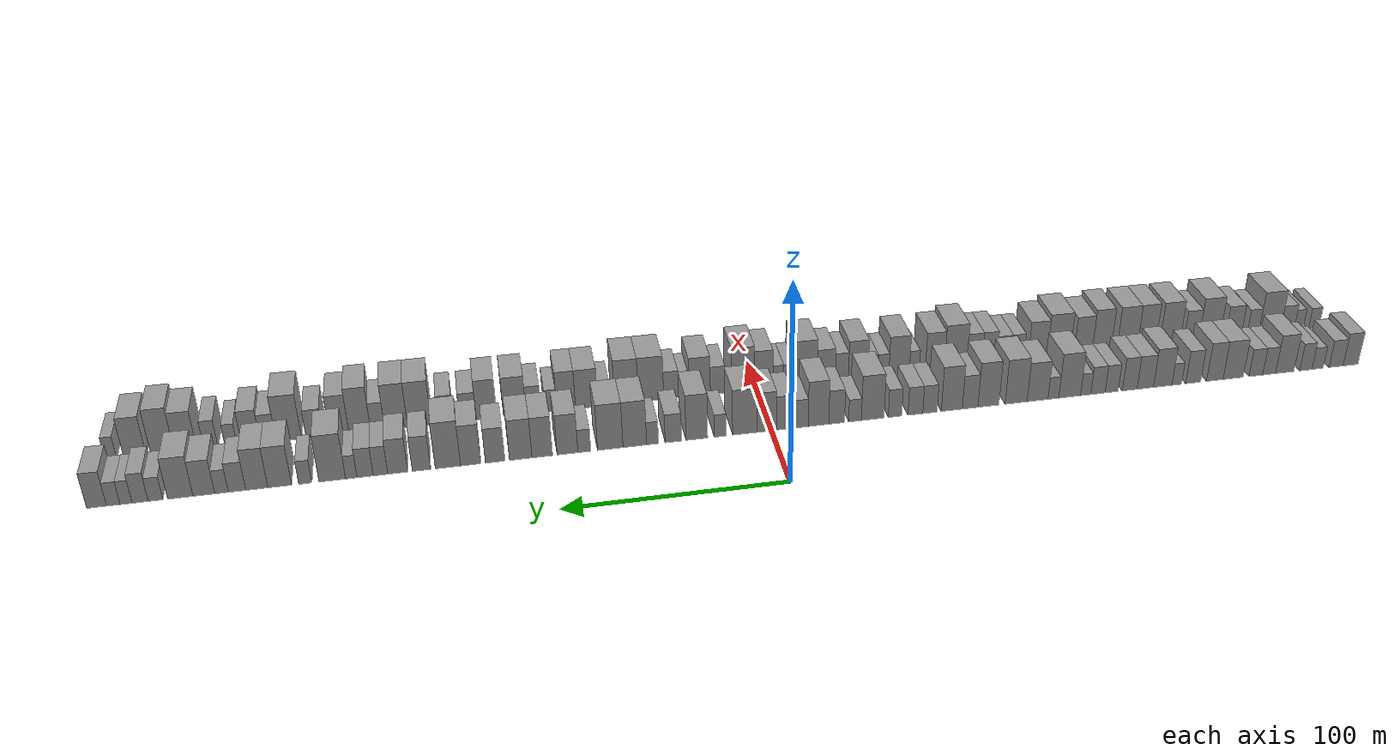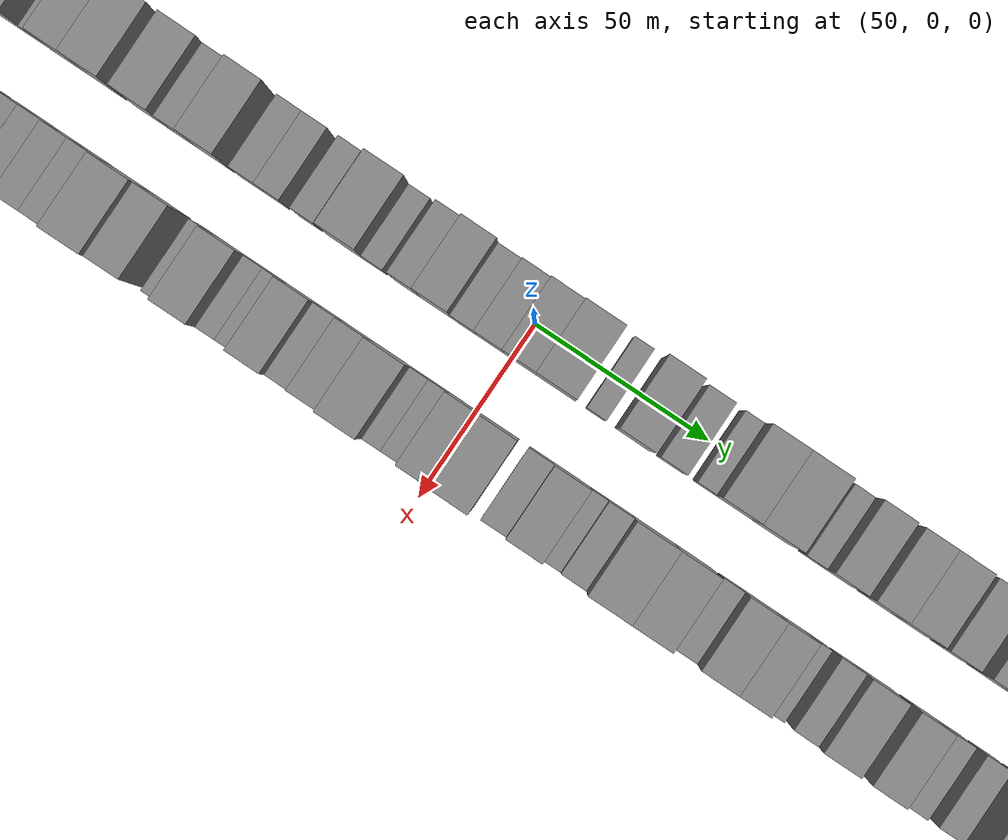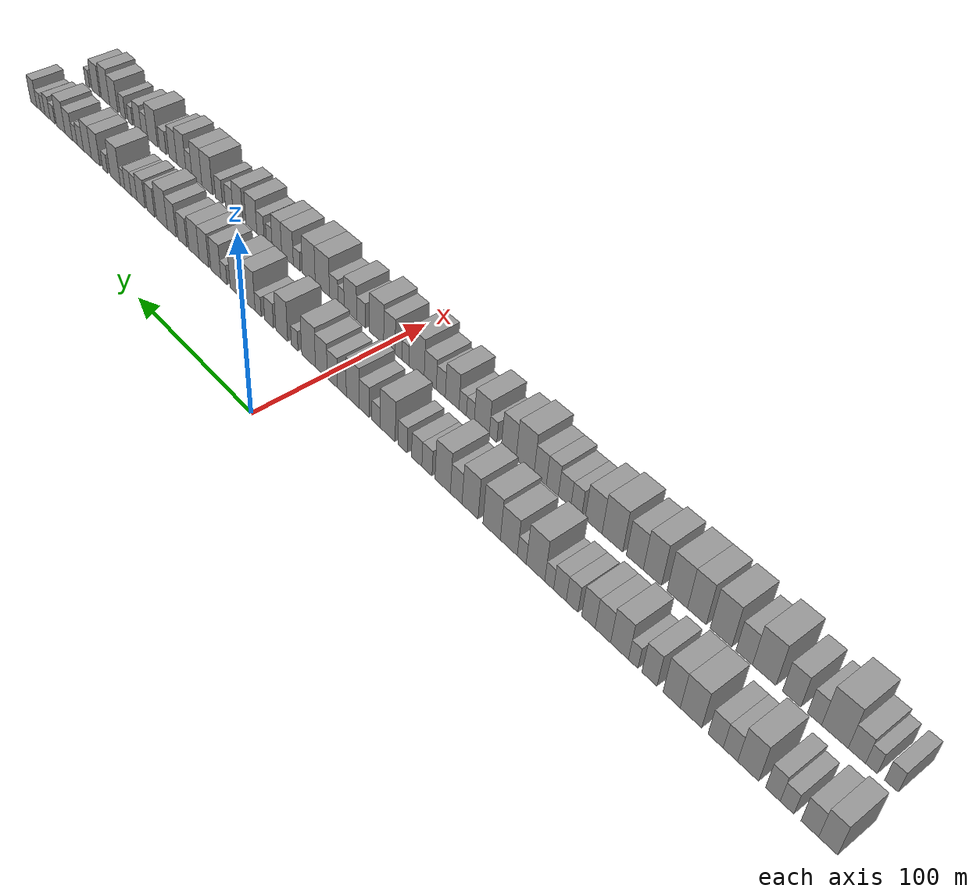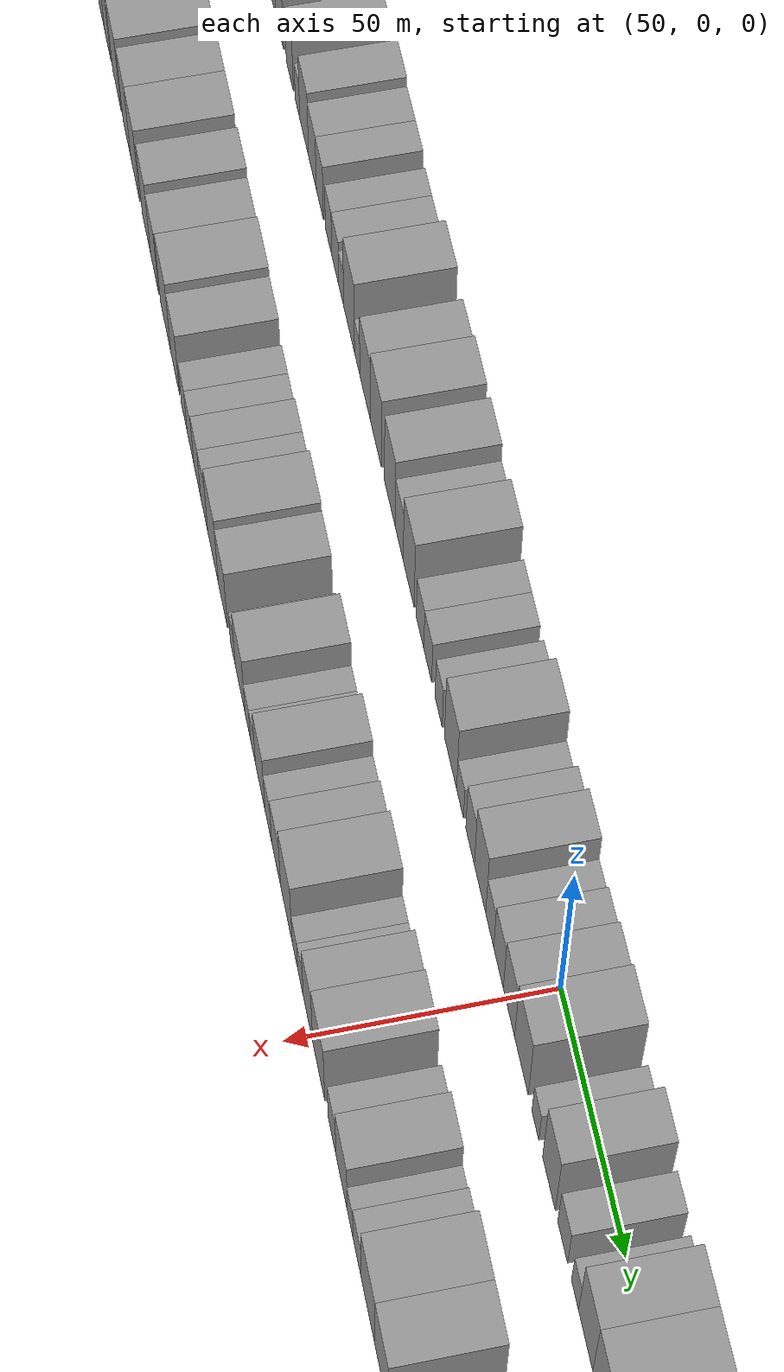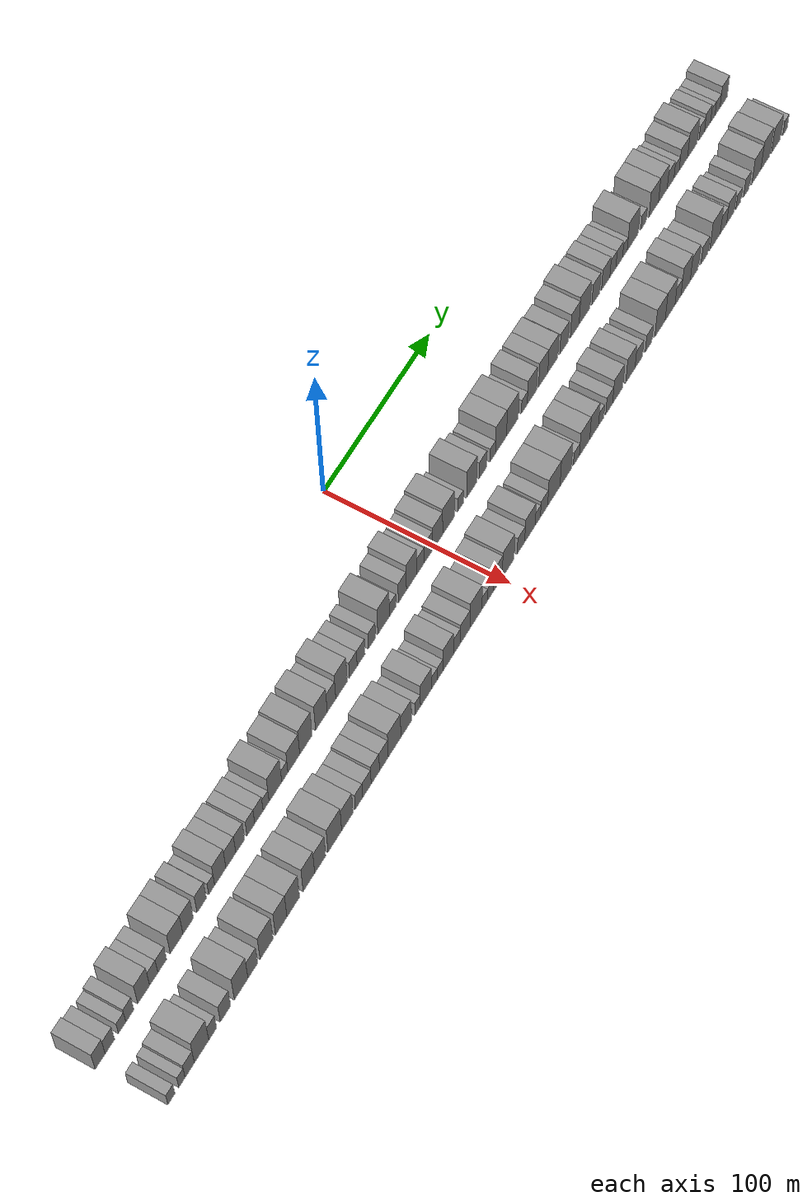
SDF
<sdf version="1.6">
 <world name="default">
  <scene>
   <sky><clouds><speed>12</speed></clouds></sky>
   <ambient>0.4 0.4 0.4 1</ambient>
   <background>0.7 0.7 0.7 1</background>
   <shadows>1</shadows>
  </scene>
  <gravity>0 0 -9.8066</gravity>
  <magnetic_field>6e-06 2.3e-05 -4.2e-05</magnetic_field>
  <physics default="0" name="default_physics" type="ode">
   <ode>
    <solver>
     <type>quick</type>
     <iters>10</iters>
     <sor>1.0</sor>
     <use_dynamic_moi_rescaling>0</use_dynamic_moi_rescaling>
    </solver>
    <constraints>
     <cfm>0</cfm>
     <erp>0.2</erp>
     <contact_max_correcting_vel>100</contact_max_correcting_vel>
     <contact_surface_layer>0.001</contact_surface_layer>
    </constraints>
   </ode>
   <max_step_size>0.004</max_step_size>
   <real_time_factor>1</real_time_factor>
   <real_time_update_rate>250</real_time_update_rate>
  </physics>
  <light name="sun" type="directional">
   <pose>0 0 10 0 0 0</pose>
   <diffuse>0.8 0.8 0.8 1</diffuse>
   <specular>0.2 0.2 0.2 1</specular>
   <attenuation>
    <range>1000</range>
    <constant>0.9</constant>
    <linear>0.01</linear>
    <quadratic>0.001</quadratic>
   </attenuation>
   <direction>-0.5 0.1 -0.9</direction>
  </light>
  <model name="building_1">
   <static>1</static>
   <pose>50.0000 -286.0675 0 0.000000 0.000000 0.000000</pose>
   <link name="link">
    <pose>0 0 9.00 0 0 0</pose>
    <collision name="collision"><geometry><box><size>20.0000 7.8650 18.0000</size></box></geometry></collision>
    <visual name="visual">
     <cast_shadows>0</cast_shadows>
     <geometry><box><size>20.0000 7.8650 18.0000</size></box></geometry>
     <material>
      <script>
       <uri>model://grey_wall/materials/scripts</uri>
       <uri>model://grey_wall/materials/textures</uri>
       <name>vrc/grey_wall</name>
      </script>
     </material>
    </visual>
   </link>
  </model>
  <model name="building_2">
   <static>1</static>
   <pose>50.0000 -278.4291 0 0.000000 0.000000 0.000000</pose>
   <link name="link">
    <pose>0 0 7.50 0 0 0</pose>
    <collision name="collision"><geometry><box><size>20.0000 7.4119 15.0000</size></box></geometry></collision>
    <visual name="visual">
     <cast_shadows>0</cast_shadows>
     <geometry><box><size>20.0000 7.4119 15.0000</size></box></geometry>
     <material>
      <script>
       <uri>model://grey_wall/materials/scripts</uri>
       <uri>model://grey_wall/materials/textures</uri>
       <name>vrc/grey_wall</name>
      </script>
     </material>
    </visual>
   </link>
  </model>
  <model name="building_3">
   <static>1</static>
   <pose>50.0000 -268.7812 0 0.000000 0.000000 0.000000</pose>
   <link name="link">
    <pose>0 0 6.00 0 0 0</pose>
    <collision name="collision"><geometry><box><size>20.0000 5.8838 12.0000</size></box></geometry></collision>
    <visual name="visual">
     <cast_shadows>0</cast_shadows>
     <geometry><box><size>20.0000 5.8838 12.0000</size></box></geometry>
     <material>
      <script>
       <uri>model://grey_wall/materials/scripts</uri>
       <uri>model://grey_wall/materials/textures</uri>
       <name>vrc/grey_wall</name>
      </script>
     </material>
    </visual>
   </link>
  </model>
  <model name="building_4">
   <static>1</static>
   <pose>50.0000 -262.6302 0 0.000000 0.000000 0.000000</pose>
   <link name="link">
    <pose>0 0 7.50 0 0 0</pose>
    <collision name="collision"><geometry><box><size>20.0000 6.4182 15.0000</size></box></geometry></collision>
    <visual name="visual">
     <cast_shadows>0</cast_shadows>
     <geometry><box><size>20.0000 6.4182 15.0000</size></box></geometry>
     <material>
      <script>
       <uri>model://grey_wall/materials/scripts</uri>
       <uri>model://grey_wall/materials/textures</uri>
       <name>vrc/grey_wall</name>
      </script>
     </material>
    </visual>
   </link>
  </model>
  <model name="building_5">
   <static>1</static>
   <pose>50.0000 -251.6688 0 0.000000 0.000000 0.000000</pose>
   <link name="link">
    <pose>0 0 10.50 0 0 0</pose>
    <collision name="collision"><geometry><box><size>20.0000 9.5047 21.0000</size></box></geometry></collision>
    <visual name="visual">
     <cast_shadows>0</cast_shadows>
     <geometry><box><size>20.0000 9.5047 21.0000</size></box></geometry>
     <material>
      <script>
       <uri>model://grey_wall/materials/scripts</uri>
       <uri>model://grey_wall/materials/textures</uri>
       <name>vrc/grey_wall</name>
      </script>
     </material>
    </visual>
   </link>
  </model>
  <model name="building_6">
   <static>1</static>
   <pose>50.0000 -243.5959 0 0.000000 0.000000 0.000000</pose>
   <link name="link">
    <pose>0 0 7.50 0 0 0</pose>
    <collision name="collision"><geometry><box><size>20.0000 6.6412 15.0000</size></box></geometry></collision>
    <visual name="visual">
     <cast_shadows>0</cast_shadows>
     <geometry><box><size>20.0000 6.6412 15.0000</size></box></geometry>
     <material>
      <script>
       <uri>model://grey_wall/materials/scripts</uri>
       <uri>model://grey_wall/materials/textures</uri>
       <name>vrc/grey_wall</name>
      </script>
     </material>
    </visual>
   </link>
  </model>
  <model name="building_7">
   <static>1</static>
   <pose>50.0000 -236.7432 0 0.000000 0.000000 0.000000</pose>
   <link name="link">
    <pose>0 0 7.50 0 0 0</pose>
    <collision name="collision"><geometry><box><size>20.0000 7.0642 15.0000</size></box></geometry></collision>
    <visual name="visual">
     <cast_shadows>0</cast_shadows>
     <geometry><box><size>20.0000 7.0642 15.0000</size></box></geometry>
     <material>
      <script>
       <uri>model://grey_wall/materials/scripts</uri>
       <uri>model://grey_wall/materials/textures</uri>
       <name>vrc/grey_wall</name>
      </script>
     </material>
    </visual>
   </link>
  </model>
  <model name="building_8">
   <static>1</static>
   <pose>50.0000 -225.0730 0 0.000000 0.000000 0.000000</pose>
   <link name="link">
    <pose>0 0 10.50 0 0 0</pose>
    <collision name="collision"><geometry><box><size>20.0000 10.2760 21.0000</size></box></geometry></collision>
    <visual name="visual">
     <cast_shadows>0</cast_shadows>
     <geometry><box><size>20.0000 10.2760 21.0000</size></box></geometry>
     <material>
      <script>
       <uri>model://grey_wall/materials/scripts</uri>
       <uri>model://grey_wall/materials/textures</uri>
       <name>vrc/grey_wall</name>
      </script>
     </material>
    </visual>
   </link>
  </model>
  <model name="building_9">
   <static>1</static>
   <pose>50.0000 -215.6762 0 0.000000 0.000000 0.000000</pose>
   <link name="link">
    <pose>0 0 10.50 0 0 0</pose>
    <collision name="collision"><geometry><box><size>20.0000 8.5176 21.0000</size></box></geometry></collision>
    <visual name="visual">
     <cast_shadows>0</cast_shadows>
     <geometry><box><size>20.0000 8.5176 21.0000</size></box></geometry>
     <material>
      <script>
       <uri>model://grey_wall/materials/scripts</uri>
       <uri>model://grey_wall/materials/textures</uri>
       <name>vrc/grey_wall</name>
      </script>
     </material>
    </visual>
   </link>
  </model>
  <model name="building_10">
   <static>1</static>
   <pose>50.0000 -204.5940 0 0.000000 0.000000 0.000000</pose>
   <link name="link">
    <pose>0 0 9.00 0 0 0</pose>
    <collision name="collision"><geometry><box><size>20.0000 7.6467 18.0000</size></box></geometry></collision>
    <visual name="visual">
     <cast_shadows>0</cast_shadows>
     <geometry><box><size>20.0000 7.6467 18.0000</size></box></geometry>
     <material>
      <script>
       <uri>model://grey_wall/materials/scripts</uri>
       <uri>model://grey_wall/materials/textures</uri>
       <name>vrc/grey_wall</name>
      </script>
     </material>
    </visual>
   </link>
  </model>
  <model name="building_11">
   <static>1</static>
   <pose>50.0000 -196.3125 0 0.000000 0.000000 0.000000</pose>
   <link name="link">
    <pose>0 0 6.00 0 0 0</pose>
    <collision name="collision"><geometry><box><size>20.0000 4.9163 12.0000</size></box></geometry></collision>
    <visual name="visual">
     <cast_shadows>0</cast_shadows>
     <geometry><box><size>20.0000 4.9163 12.0000</size></box></geometry>
     <material>
      <script>
       <uri>model://grey_wall/materials/scripts</uri>
       <uri>model://grey_wall/materials/textures</uri>
       <name>vrc/grey_wall</name>
      </script>
     </material>
    </visual>
   </link>
  </model>
  <model name="building_12">
   <static>1</static>
   <pose>50.0000 -189.1845 0 0.000000 0.000000 0.000000</pose>
   <link name="link">
    <pose>0 0 10.50 0 0 0</pose>
    <collision name="collision"><geometry><box><size>20.0000 9.3396 21.0000</size></box></geometry></collision>
    <visual name="visual">
     <cast_shadows>0</cast_shadows>
     <geometry><box><size>20.0000 9.3396 21.0000</size></box></geometry>
     <material>
      <script>
       <uri>model://grey_wall/materials/scripts</uri>
       <uri>model://grey_wall/materials/textures</uri>
       <name>vrc/grey_wall</name>
      </script>
     </material>
    </visual>
   </link>
  </model>
  <model name="building_13">
   <static>1</static>
   <pose>50.0000 -180.3806 0 0.000000 0.000000 0.000000</pose>
   <link name="link">
    <pose>0 0 9.00 0 0 0</pose>
    <collision name="collision"><geometry><box><size>20.0000 8.2682 18.0000</size></box></geometry></collision>
    <visual name="visual">
     <cast_shadows>0</cast_shadows>
     <geometry><box><size>20.0000 8.2682 18.0000</size></box></geometry>
     <material>
      <script>
       <uri>model://grey_wall/materials/scripts</uri>
       <uri>model://grey_wall/materials/textures</uri>
       <name>vrc/grey_wall</name>
      </script>
     </material>
    </visual>
   </link>
  </model>
  <model name="building_14">
   <static>1</static>
   <pose>50.0000 -172.5509 0 0.000000 0.000000 0.000000</pose>
   <link name="link">
    <pose>0 0 9.00 0 0 0</pose>
    <collision name="collision"><geometry><box><size>20.0000 7.3913 18.0000</size></box></geometry></collision>
    <visual name="visual">
     <cast_shadows>0</cast_shadows>
     <geometry><box><size>20.0000 7.3913 18.0000</size></box></geometry>
     <material>
      <script>
       <uri>model://grey_wall/materials/scripts</uri>
       <uri>model://grey_wall/materials/textures</uri>
       <name>vrc/grey_wall</name>
      </script>
     </material>
    </visual>
   </link>
  </model>
  <model name="building_15">
   <static>1</static>
   <pose>50.0000 -163.5788 0 0.000000 0.000000 0.000000</pose>
   <link name="link">
    <pose>0 0 7.50 0 0 0</pose>
    <collision name="collision"><geometry><box><size>20.0000 6.5529 15.0000</size></box></geometry></collision>
    <visual name="visual">
     <cast_shadows>0</cast_shadows>
     <geometry><box><size>20.0000 6.5529 15.0000</size></box></geometry>
     <material>
      <script>
       <uri>model://grey_wall/materials/scripts</uri>
       <uri>model://grey_wall/materials/textures</uri>
       <name>vrc/grey_wall</name>
      </script>
     </material>
    </visual>
   </link>
  </model>
  <model name="building_16">
   <static>1</static>
   <pose>50.0000 -156.7487 0 0.000000 0.000000 0.000000</pose>
   <link name="link">
    <pose>0 0 7.50 0 0 0</pose>
    <collision name="collision"><geometry><box><size>20.0000 7.1074 15.0000</size></box></geometry></collision>
    <visual name="visual">
     <cast_shadows>0</cast_shadows>
     <geometry><box><size>20.0000 7.1074 15.0000</size></box></geometry>
     <material>
      <script>
       <uri>model://grey_wall/materials/scripts</uri>
       <uri>model://grey_wall/materials/textures</uri>
       <name>vrc/grey_wall</name>
      </script>
     </material>
    </visual>
   </link>
  </model>
  <model name="building_17">
   <static>1</static>
   <pose>50.0000 -150.6562 0 0.000000 0.000000 0.000000</pose>
   <link name="link">
    <pose>0 0 6.00 0 0 0</pose>
    <collision name="collision"><geometry><box><size>20.0000 5.0775 12.0000</size></box></geometry></collision>
    <visual name="visual">
     <cast_shadows>0</cast_shadows>
     <geometry><box><size>20.0000 5.0775 12.0000</size></box></geometry>
     <material>
      <script>
       <uri>model://grey_wall/materials/scripts</uri>
       <uri>model://grey_wall/materials/textures</uri>
       <name>vrc/grey_wall</name>
      </script>
     </material>
    </visual>
   </link>
  </model>
  <model name="building_18">
   <static>1</static>
   <pose>50.0000 -142.7013 0 0.000000 0.000000 0.000000</pose>
   <link name="link">
    <pose>0 0 12.00 0 0 0</pose>
    <collision name="collision"><geometry><box><size>20.0000 10.8324 24.0000</size></box></geometry></collision>
    <visual name="visual">
     <cast_shadows>0</cast_shadows>
     <geometry><box><size>20.0000 10.8324 24.0000</size></box></geometry>
     <material>
      <script>
       <uri>model://grey_wall/materials/scripts</uri>
       <uri>model://grey_wall/materials/textures</uri>
       <name>vrc/grey_wall</name>
      </script>
     </material>
    </visual>
   </link>
  </model>
  <model name="building_19">
   <static>1</static>
   <pose>50.0000 -134.6364 0 0.000000 0.000000 0.000000</pose>
   <link name="link">
    <pose>0 0 6.00 0 0 0</pose>
    <collision name="collision"><geometry><box><size>20.0000 5.2974 12.0000</size></box></geometry></collision>
    <visual name="visual">
     <cast_shadows>0</cast_shadows>
     <geometry><box><size>20.0000 5.2974 12.0000</size></box></geometry>
     <material>
      <script>
       <uri>model://grey_wall/materials/scripts</uri>
       <uri>model://grey_wall/materials/textures</uri>
       <name>vrc/grey_wall</name>
      </script>
     </material>
    </visual>
   </link>
  </model>
  <model name="building_20">
   <static>1</static>
   <pose>50.0000 -126.8587 0 0.000000 0.000000 0.000000</pose>
   <link name="link">
    <pose>0 0 10.50 0 0 0</pose>
    <collision name="collision"><geometry><box><size>20.0000 10.2580 21.0000</size></box></geometry></collision>
    <visual name="visual">
     <cast_shadows>0</cast_shadows>
     <geometry><box><size>20.0000 10.2580 21.0000</size></box></geometry>
     <material>
      <script>
       <uri>model://grey_wall/materials/scripts</uri>
       <uri>model://grey_wall/materials/textures</uri>
       <name>vrc/grey_wall</name>
      </script>
     </material>
    </visual>
   </link>
  </model>
  <model name="building_21">
   <static>1</static>
   <pose>50.0000 -116.3486 0 0.000000 0.000000 0.000000</pose>
   <link name="link">
    <pose>0 0 12.00 0 0 0</pose>
    <collision name="collision"><geometry><box><size>20.0000 10.7622 24.0000</size></box></geometry></collision>
    <visual name="visual">
     <cast_shadows>0</cast_shadows>
     <geometry><box><size>20.0000 10.7622 24.0000</size></box></geometry>
     <material>
      <script>
       <uri>model://grey_wall/materials/scripts</uri>
       <uri>model://grey_wall/materials/textures</uri>
       <name>vrc/grey_wall</name>
      </script>
     </material>
    </visual>
   </link>
  </model>
  <model name="building_22">
   <static>1</static>
   <pose>50.0000 -102.8429 0 0.000000 0.000000 0.000000</pose>
   <link name="link">
    <pose>0 0 12.00 0 0 0</pose>
    <collision name="collision"><geometry><box><size>20.0000 10.2493 24.0000</size></box></geometry></collision>
    <visual name="visual">
     <cast_shadows>0</cast_shadows>
     <geometry><box><size>20.0000 10.2493 24.0000</size></box></geometry>
     <material>
      <script>
       <uri>model://grey_wall/materials/scripts</uri>
       <uri>model://grey_wall/materials/textures</uri>
       <name>vrc/grey_wall</name>
      </script>
     </material>
    </visual>
   </link>
  </model>
  <model name="building_23">
   <static>1</static>
   <pose>50.0000 -93.9561 0 0.000000 0.000000 0.000000</pose>
   <link name="link">
    <pose>0 0 9.00 0 0 0</pose>
    <collision name="collision"><geometry><box><size>20.0000 7.5243 18.0000</size></box></geometry></collision>
    <visual name="visual">
     <cast_shadows>0</cast_shadows>
     <geometry><box><size>20.0000 7.5243 18.0000</size></box></geometry>
     <material>
      <script>
       <uri>model://grey_wall/materials/scripts</uri>
       <uri>model://grey_wall/materials/textures</uri>
       <name>vrc/grey_wall</name>
      </script>
     </material>
    </visual>
   </link>
  </model>
  <model name="building_24">
   <static>1</static>
   <pose>50.0000 -85.1088 0 0.000000 0.000000 0.000000</pose>
   <link name="link">
    <pose>0 0 12.00 0 0 0</pose>
    <collision name="collision"><geometry><box><size>20.0000 10.1702 24.0000</size></box></geometry></collision>
    <visual name="visual">
     <cast_shadows>0</cast_shadows>
     <geometry><box><size>20.0000 10.1702 24.0000</size></box></geometry>
     <material>
      <script>
       <uri>model://grey_wall/materials/scripts</uri>
       <uri>model://grey_wall/materials/textures</uri>
       <name>vrc/grey_wall</name>
      </script>
     </material>
    </visual>
   </link>
  </model>
  <model name="building_25">
   <static>1</static>
   <pose>50.0000 -74.5990 0 0.000000 0.000000 0.000000</pose>
   <link name="link">
    <pose>0 0 7.50 0 0 0</pose>
    <collision name="collision"><geometry><box><size>20.0000 6.8495 15.0000</size></box></geometry></collision>
    <visual name="visual">
     <cast_shadows>0</cast_shadows>
     <geometry><box><size>20.0000 6.8495 15.0000</size></box></geometry>
     <material>
      <script>
       <uri>model://grey_wall/materials/scripts</uri>
       <uri>model://grey_wall/materials/textures</uri>
       <name>vrc/grey_wall</name>
      </script>
     </material>
    </visual>
   </link>
  </model>
  <model name="building_26">
   <static>1</static>
   <pose>50.0000 -67.6113 0 0.000000 0.000000 0.000000</pose>
   <link name="link">
    <pose>0 0 7.50 0 0 0</pose>
    <collision name="collision"><geometry><box><size>20.0000 7.1259 15.0000</size></box></geometry></collision>
    <visual name="visual">
     <cast_shadows>0</cast_shadows>
     <geometry><box><size>20.0000 7.1259 15.0000</size></box></geometry>
     <material>
      <script>
       <uri>model://grey_wall/materials/scripts</uri>
       <uri>model://grey_wall/materials/textures</uri>
       <name>vrc/grey_wall</name>
      </script>
     </material>
    </visual>
   </link>
  </model>
  <model name="building_27">
   <static>1</static>
   <pose>50.0000 -57.8400 0 0.000000 0.000000 0.000000</pose>
   <link name="link">
    <pose>0 0 7.50 0 0 0</pose>
    <collision name="collision"><geometry><box><size>20.0000 6.4167 15.0000</size></box></geometry></collision>
    <visual name="visual">
     <cast_shadows>0</cast_shadows>
     <geometry><box><size>20.0000 6.4167 15.0000</size></box></geometry>
     <material>
      <script>
       <uri>model://grey_wall/materials/scripts</uri>
       <uri>model://grey_wall/materials/textures</uri>
       <name>vrc/grey_wall</name>
      </script>
     </material>
    </visual>
   </link>
  </model>
  <model name="building_28">
   <static>1</static>
   <pose>50.0000 -47.2532 0 0.000000 0.000000 0.000000</pose>
   <link name="link">
    <pose>0 0 12.00 0 0 0</pose>
    <collision name="collision"><geometry><box><size>20.0000 10.7568 24.0000</size></box></geometry></collision>
    <visual name="visual">
     <cast_shadows>0</cast_shadows>
     <geometry><box><size>20.0000 10.7568 24.0000</size></box></geometry>
     <material>
      <script>
       <uri>model://grey_wall/materials/scripts</uri>
       <uri>model://grey_wall/materials/textures</uri>
       <name>vrc/grey_wall</name>
      </script>
     </material>
    </visual>
   </link>
  </model>
  <model name="building_29">
   <static>1</static>
   <pose>50.0000 -38.8885 0 0.000000 0.000000 0.000000</pose>
   <link name="link">
    <pose>0 0 6.00 0 0 0</pose>
    <collision name="collision"><geometry><box><size>20.0000 5.9726 12.0000</size></box></geometry></collision>
    <visual name="visual">
     <cast_shadows>0</cast_shadows>
     <geometry><box><size>20.0000 5.9726 12.0000</size></box></geometry>
     <material>
      <script>
       <uri>model://grey_wall/materials/scripts</uri>
       <uri>model://grey_wall/materials/textures</uri>
       <name>vrc/grey_wall</name>
      </script>
     </material>
    </visual>
   </link>
  </model>
  <model name="building_30">
   <static>1</static>
   <pose>50.0000 -30.2129 0 0.000000 0.000000 0.000000</pose>
   <link name="link">
    <pose>0 0 9.00 0 0 0</pose>
    <collision name="collision"><geometry><box><size>20.0000 7.3786 18.0000</size></box></geometry></collision>
    <visual name="visual">
     <cast_shadows>0</cast_shadows>
     <geometry><box><size>20.0000 7.3786 18.0000</size></box></geometry>
     <material>
      <script>
       <uri>model://grey_wall/materials/scripts</uri>
       <uri>model://grey_wall/materials/textures</uri>
       <name>vrc/grey_wall</name>
      </script>
     </material>
    </visual>
   </link>
  </model>
  <model name="building_31">
   <static>1</static>
   <pose>50.0000 -21.6969 0 0.000000 0.000000 0.000000</pose>
   <link name="link">
    <pose>0 0 12.00 0 0 0</pose>
    <collision name="collision"><geometry><box><size>20.0000 9.6533 24.0000</size></box></geometry></collision>
    <visual name="visual">
     <cast_shadows>0</cast_shadows>
     <geometry><box><size>20.0000 9.6533 24.0000</size></box></geometry>
     <material>
      <script>
       <uri>model://grey_wall/materials/scripts</uri>
       <uri>model://grey_wall/materials/textures</uri>
       <name>vrc/grey_wall</name>
      </script>
     </material>
    </visual>
   </link>
  </model>
  <model name="building_32">
   <static>1</static>
   <pose>50.0000 -13.5113 0 0.000000 0.000000 0.000000</pose>
   <link name="link">
    <pose>0 0 7.50 0 0 0</pose>
    <collision name="collision"><geometry><box><size>20.0000 6.7177 15.0000</size></box></geometry></collision>
    <visual name="visual">
     <cast_shadows>0</cast_shadows>
     <geometry><box><size>20.0000 6.7177 15.0000</size></box></geometry>
     <material>
      <script>
       <uri>model://grey_wall/materials/scripts</uri>
       <uri>model://grey_wall/materials/textures</uri>
       <name>vrc/grey_wall</name>
      </script>
     </material>
    </visual>
   </link>
  </model>
  <model name="building_33">
   <static>1</static>
   <pose>50.0000 -6.1777 0 0.000000 0.000000 0.000000</pose>
   <link name="link">
    <pose>0 0 9.00 0 0 0</pose>
    <collision name="collision"><geometry><box><size>20.0000 7.9495 18.0000</size></box></geometry></collision>
    <visual name="visual">
     <cast_shadows>0</cast_shadows>
     <geometry><box><size>20.0000 7.9495 18.0000</size></box></geometry>
     <material>
      <script>
       <uri>model://grey_wall/materials/scripts</uri>
       <uri>model://grey_wall/materials/textures</uri>
       <name>vrc/grey_wall</name>
      </script>
     </material>
    </visual>
   </link>
  </model>
  <model name="building_34">
   <static>1</static>
   <pose>50.0000 2.4501 0 0.000000 0.000000 0.000000</pose>
   <link name="link">
    <pose>0 0 10.50 0 0 0</pose>
    <collision name="collision"><geometry><box><size>20.0000 9.3061 21.0000</size></box></geometry></collision>
    <visual name="visual">
     <cast_shadows>0</cast_shadows>
     <geometry><box><size>20.0000 9.3061 21.0000</size></box></geometry>
     <material>
      <script>
       <uri>model://grey_wall/materials/scripts</uri>
       <uri>model://grey_wall/materials/textures</uri>
       <name>vrc/grey_wall</name>
      </script>
     </material>
    </visual>
   </link>
  </model>
  <model name="building_35">
   <static>1</static>
   <pose>50.0000 12.6278 0 0.000000 0.000000 0.000000</pose>
   <link name="link">
    <pose>0 0 12.00 0 0 0</pose>
    <collision name="collision"><geometry><box><size>20.0000 11.0493 24.0000</size></box></geometry></collision>
    <visual name="visual">
     <cast_shadows>0</cast_shadows>
     <geometry><box><size>20.0000 11.0493 24.0000</size></box></geometry>
     <material>
      <script>
       <uri>model://grey_wall/materials/scripts</uri>
       <uri>model://grey_wall/materials/textures</uri>
       <name>vrc/grey_wall</name>
      </script>
     </material>
    </visual>
   </link>
  </model>
  <model name="building_36">
   <static>1</static>
   <pose>50.0000 23.8809 0 0.000000 0.000000 0.000000</pose>
   <link name="link">
    <pose>0 0 6.00 0 0 0</pose>
    <collision name="collision"><geometry><box><size>20.0000 5.4568 12.0000</size></box></geometry></collision>
    <visual name="visual">
     <cast_shadows>0</cast_shadows>
     <geometry><box><size>20.0000 5.4568 12.0000</size></box></geometry>
     <material>
      <script>
       <uri>model://grey_wall/materials/scripts</uri>
       <uri>model://grey_wall/materials/textures</uri>
       <name>vrc/grey_wall</name>
      </script>
     </material>
    </visual>
   </link>
  </model>
  <model name="building_37">
   <static>1</static>
   <pose>50.0000 34.5633 0 0.000000 0.000000 0.000000</pose>
   <link name="link">
    <pose>0 0 12.00 0 0 0</pose>
    <collision name="collision"><geometry><box><size>20.0000 9.9080 24.0000</size></box></geometry></collision>
    <visual name="visual">
     <cast_shadows>0</cast_shadows>
     <geometry><box><size>20.0000 9.9080 24.0000</size></box></geometry>
     <material>
      <script>
       <uri>model://grey_wall/materials/scripts</uri>
       <uri>model://grey_wall/materials/textures</uri>
       <name>vrc/grey_wall</name>
      </script>
     </material>
    </visual>
   </link>
  </model>
  <model name="building_38">
   <static>1</static>
   <pose>50.0000 45.2656 0 0.000000 0.000000 0.000000</pose>
   <link name="link">
    <pose>0 0 7.50 0 0 0</pose>
    <collision name="collision"><geometry><box><size>20.0000 7.4966 15.0000</size></box></geometry></collision>
    <visual name="visual">
     <cast_shadows>0</cast_shadows>
     <geometry><box><size>20.0000 7.4966 15.0000</size></box></geometry>
     <material>
      <script>
       <uri>model://grey_wall/materials/scripts</uri>
       <uri>model://grey_wall/materials/textures</uri>
       <name>vrc/grey_wall</name>
      </script>
     </material>
    </visual>
   </link>
  </model>
  <model name="building_39">
   <static>1</static>
   <pose>50.0000 54.6989 0 0.000000 0.000000 0.000000</pose>
   <link name="link">
    <pose>0 0 6.00 0 0 0</pose>
    <collision name="collision"><geometry><box><size>20.0000 5.3701 12.0000</size></box></geometry></collision>
    <visual name="visual">
     <cast_shadows>0</cast_shadows>
     <geometry><box><size>20.0000 5.3701 12.0000</size></box></geometry>
     <material>
      <script>
       <uri>model://grey_wall/materials/scripts</uri>
       <uri>model://grey_wall/materials/textures</uri>
       <name>vrc/grey_wall</name>
      </script>
     </material>
    </visual>
   </link>
  </model>
  <model name="building_40">
   <static>1</static>
   <pose>50.0000 62.7088 0 0.000000 0.000000 0.000000</pose>
   <link name="link">
    <pose>0 0 12.00 0 0 0</pose>
    <collision name="collision"><geometry><box><size>20.0000 10.6496 24.0000</size></box></geometry></collision>
    <visual name="visual">
     <cast_shadows>0</cast_shadows>
     <geometry><box><size>20.0000 10.6496 24.0000</size></box></geometry>
     <material>
      <script>
       <uri>model://grey_wall/materials/scripts</uri>
       <uri>model://grey_wall/materials/textures</uri>
       <name>vrc/grey_wall</name>
      </script>
     </material>
    </visual>
   </link>
  </model>
  <model name="building_41">
   <static>1</static>
   <pose>50.0000 73.7607 0 0.000000 0.000000 0.000000</pose>
   <link name="link">
    <pose>0 0 12.00 0 0 0</pose>
    <collision name="collision"><geometry><box><size>20.0000 11.4543 24.0000</size></box></geometry></collision>
    <visual name="visual">
     <cast_shadows>0</cast_shadows>
     <geometry><box><size>20.0000 11.4543 24.0000</size></box></geometry>
     <material>
      <script>
       <uri>model://grey_wall/materials/scripts</uri>
       <uri>model://grey_wall/materials/textures</uri>
       <name>vrc/grey_wall</name>
      </script>
     </material>
    </visual>
   </link>
  </model>
  <model name="building_42">
   <static>1</static>
   <pose>50.0000 85.3550 0 0.000000 0.000000 0.000000</pose>
   <link name="link">
    <pose>0 0 6.00 0 0 0</pose>
    <collision name="collision"><geometry><box><size>20.0000 5.7342 12.0000</size></box></geometry></collision>
    <visual name="visual">
     <cast_shadows>0</cast_shadows>
     <geometry><box><size>20.0000 5.7342 12.0000</size></box></geometry>
     <material>
      <script>
       <uri>model://grey_wall/materials/scripts</uri>
       <uri>model://grey_wall/materials/textures</uri>
       <name>vrc/grey_wall</name>
      </script>
     </material>
    </visual>
   </link>
  </model>
  <model name="building_43">
   <static>1</static>
   <pose>50.0000 92.8432 0 0.000000 0.000000 0.000000</pose>
   <link name="link">
    <pose>0 0 10.50 0 0 0</pose>
    <collision name="collision"><geometry><box><size>20.0000 9.2423 21.0000</size></box></geometry></collision>
    <visual name="visual">
     <cast_shadows>0</cast_shadows>
     <geometry><box><size>20.0000 9.2423 21.0000</size></box></geometry>
     <material>
      <script>
       <uri>model://grey_wall/materials/scripts</uri>
       <uri>model://grey_wall/materials/textures</uri>
       <name>vrc/grey_wall</name>
      </script>
     </material>
    </visual>
   </link>
  </model>
  <model name="building_44">
   <static>1</static>
   <pose>50.0000 104.0225 0 0.000000 0.000000 0.000000</pose>
   <link name="link">
    <pose>0 0 10.50 0 0 0</pose>
    <collision name="collision"><geometry><box><size>20.0000 9.1162 21.0000</size></box></geometry></collision>
    <visual name="visual">
     <cast_shadows>0</cast_shadows>
     <geometry><box><size>20.0000 9.1162 21.0000</size></box></geometry>
     <material>
      <script>
       <uri>model://grey_wall/materials/scripts</uri>
       <uri>model://grey_wall/materials/textures</uri>
       <name>vrc/grey_wall</name>
      </script>
     </material>
    </visual>
   </link>
  </model>
  <model name="building_45">
   <static>1</static>
   <pose>50.0000 113.5234 0 0.000000 0.000000 0.000000</pose>
   <link name="link">
    <pose>0 0 10.50 0 0 0</pose>
    <collision name="collision"><geometry><box><size>20.0000 9.8857 21.0000</size></box></geometry></collision>
    <visual name="visual">
     <cast_shadows>0</cast_shadows>
     <geometry><box><size>20.0000 9.8857 21.0000</size></box></geometry>
     <material>
      <script>
       <uri>model://grey_wall/materials/scripts</uri>
       <uri>model://grey_wall/materials/textures</uri>
       <name>vrc/grey_wall</name>
      </script>
     </material>
    </visual>
   </link>
  </model>
  <model name="building_46">
   <static>1</static>
   <pose>50.0000 124.7438 0 0.000000 0.000000 0.000000</pose>
   <link name="link">
    <pose>0 0 9.00 0 0 0</pose>
    <collision name="collision"><geometry><box><size>20.0000 8.5551 18.0000</size></box></geometry></collision>
    <visual name="visual">
     <cast_shadows>0</cast_shadows>
     <geometry><box><size>20.0000 8.5551 18.0000</size></box></geometry>
     <material>
      <script>
       <uri>model://grey_wall/materials/scripts</uri>
       <uri>model://grey_wall/materials/textures</uri>
       <name>vrc/grey_wall</name>
      </script>
     </material>
    </visual>
   </link>
  </model>
  <model name="building_47">
   <static>1</static>
   <pose>50.0000 135.4320 0 0.000000 0.000000 0.000000</pose>
   <link name="link">
    <pose>0 0 10.50 0 0 0</pose>
    <collision name="collision"><geometry><box><size>20.0000 8.8213 21.0000</size></box></geometry></collision>
    <visual name="visual">
     <cast_shadows>0</cast_shadows>
     <geometry><box><size>20.0000 8.8213 21.0000</size></box></geometry>
     <material>
      <script>
       <uri>model://grey_wall/materials/scripts</uri>
       <uri>model://grey_wall/materials/textures</uri>
       <name>vrc/grey_wall</name>
      </script>
     </material>
    </visual>
   </link>
  </model>
  <model name="building_48">
   <static>1</static>
   <pose>50.0000 145.3478 0 0.000000 0.000000 0.000000</pose>
   <link name="link">
    <pose>0 0 12.00 0 0 0</pose>
    <collision name="collision"><geometry><box><size>20.0000 11.0102 24.0000</size></box></geometry></collision>
    <visual name="visual">
     <cast_shadows>0</cast_shadows>
     <geometry><box><size>20.0000 11.0102 24.0000</size></box></geometry>
     <material>
      <script>
       <uri>model://grey_wall/materials/scripts</uri>
       <uri>model://grey_wall/materials/textures</uri>
       <name>vrc/grey_wall</name>
      </script>
     </material>
    </visual>
   </link>
  </model>
  <model name="building_49">
   <static>1</static>
   <pose>50.0000 156.7996 0 0.000000 0.000000 0.000000</pose>
   <link name="link">
    <pose>0 0 9.00 0 0 0</pose>
    <collision name="collision"><geometry><box><size>20.0000 7.8934 18.0000</size></box></geometry></collision>
    <visual name="visual">
     <cast_shadows>0</cast_shadows>
     <geometry><box><size>20.0000 7.8934 18.0000</size></box></geometry>
     <material>
      <script>
       <uri>model://grey_wall/materials/scripts</uri>
       <uri>model://grey_wall/materials/textures</uri>
       <name>vrc/grey_wall</name>
      </script>
     </material>
    </visual>
   </link>
  </model>
  <model name="building_50">
   <static>1</static>
   <pose>50.0000 167.0324 0 0.000000 0.000000 0.000000</pose>
   <link name="link">
    <pose>0 0 9.00 0 0 0</pose>
    <collision name="collision"><geometry><box><size>20.0000 8.5721 18.0000</size></box></geometry></collision>
    <visual name="visual">
     <cast_shadows>0</cast_shadows>
     <geometry><box><size>20.0000 8.5721 18.0000</size></box></geometry>
     <material>
      <script>
       <uri>model://grey_wall/materials/scripts</uri>
       <uri>model://grey_wall/materials/textures</uri>
       <name>vrc/grey_wall</name>
      </script>
     </material>
    </visual>
   </link>
  </model>
  <model name="building_51">
   <static>1</static>
   <pose>50.0000 174.4171 0 0.000000 0.000000 0.000000</pose>
   <link name="link">
    <pose>0 0 7.50 0 0 0</pose>
    <collision name="collision"><geometry><box><size>20.0000 6.1974 15.0000</size></box></geometry></collision>
    <visual name="visual">
     <cast_shadows>0</cast_shadows>
     <geometry><box><size>20.0000 6.1974 15.0000</size></box></geometry>
     <material>
      <script>
       <uri>model://grey_wall/materials/scripts</uri>
       <uri>model://grey_wall/materials/textures</uri>
       <name>vrc/grey_wall</name>
      </script>
     </material>
    </visual>
   </link>
  </model>
  <model name="building_52">
   <static>1</static>
   <pose>50.0000 180.9856 0 0.000000 0.000000 0.000000</pose>
   <link name="link">
    <pose>0 0 7.50 0 0 0</pose>
    <collision name="collision"><geometry><box><size>20.0000 6.9395 15.0000</size></box></geometry></collision>
    <visual name="visual">
     <cast_shadows>0</cast_shadows>
     <geometry><box><size>20.0000 6.9395 15.0000</size></box></geometry>
     <material>
      <script>
       <uri>model://grey_wall/materials/scripts</uri>
       <uri>model://grey_wall/materials/textures</uri>
       <name>vrc/grey_wall</name>
      </script>
     </material>
    </visual>
   </link>
  </model>
  <model name="building_53">
   <static>1</static>
   <pose>50.0000 186.8842 0 0.000000 0.000000 0.000000</pose>
   <link name="link">
    <pose>0 0 6.00 0 0 0</pose>
    <collision name="collision"><geometry><box><size>20.0000 4.8578 12.0000</size></box></geometry></collision>
    <visual name="visual">
     <cast_shadows>0</cast_shadows>
     <geometry><box><size>20.0000 4.8578 12.0000</size></box></geometry>
     <material>
      <script>
       <uri>model://grey_wall/materials/scripts</uri>
       <uri>model://grey_wall/materials/textures</uri>
       <name>vrc/grey_wall</name>
      </script>
     </material>
    </visual>
   </link>
  </model>
  <model name="building_54">
   <static>1</static>
   <pose>50.0000 194.9506 0 0.000000 0.000000 0.000000</pose>
   <link name="link">
    <pose>0 0 12.00 0 0 0</pose>
    <collision name="collision"><geometry><box><size>20.0000 11.2751 24.0000</size></box></geometry></collision>
    <visual name="visual">
     <cast_shadows>0</cast_shadows>
     <geometry><box><size>20.0000 11.2751 24.0000</size></box></geometry>
     <material>
      <script>
       <uri>model://grey_wall/materials/scripts</uri>
       <uri>model://grey_wall/materials/textures</uri>
       <name>vrc/grey_wall</name>
      </script>
     </material>
    </visual>
   </link>
  </model>
  <model name="building_55">
   <static>1</static>
   <pose>50.0000 206.3597 0 0.000000 0.000000 0.000000</pose>
   <link name="link">
    <pose>0 0 6.00 0 0 0</pose>
    <collision name="collision"><geometry><box><size>20.0000 5.5430 12.0000</size></box></geometry></collision>
    <visual name="visual">
     <cast_shadows>0</cast_shadows>
     <geometry><box><size>20.0000 5.5430 12.0000</size></box></geometry>
     <material>
      <script>
       <uri>model://grey_wall/materials/scripts</uri>
       <uri>model://grey_wall/materials/textures</uri>
       <name>vrc/grey_wall</name>
      </script>
     </material>
    </visual>
   </link>
  </model>
  <model name="building_56">
   <static>1</static>
   <pose>50.0000 217.1143 0 0.000000 0.000000 0.000000</pose>
   <link name="link">
    <pose>0 0 10.50 0 0 0</pose>
    <collision name="collision"><geometry><box><size>20.0000 9.9661 21.0000</size></box></geometry></collision>
    <visual name="visual">
     <cast_shadows>0</cast_shadows>
     <geometry><box><size>20.0000 9.9661 21.0000</size></box></geometry>
     <material>
      <script>
       <uri>model://grey_wall/materials/scripts</uri>
       <uri>model://grey_wall/materials/textures</uri>
       <name>vrc/grey_wall</name>
      </script>
     </material>
    </visual>
   </link>
  </model>
  <model name="building_57">
   <static>1</static>
   <pose>50.0000 226.7115 0 0.000000 0.000000 0.000000</pose>
   <link name="link">
    <pose>0 0 10.50 0 0 0</pose>
    <collision name="collision"><geometry><box><size>20.0000 9.2283 21.0000</size></box></geometry></collision>
    <visual name="visual">
     <cast_shadows>0</cast_shadows>
     <geometry><box><size>20.0000 9.2283 21.0000</size></box></geometry>
     <material>
      <script>
       <uri>model://grey_wall/materials/scripts</uri>
       <uri>model://grey_wall/materials/textures</uri>
       <name>vrc/grey_wall</name>
      </script>
     </material>
    </visual>
   </link>
  </model>
  <model name="building_58">
   <static>1</static>
   <pose>50.0000 234.9569 0 0.000000 0.000000 0.000000</pose>
   <link name="link">
    <pose>0 0 7.50 0 0 0</pose>
    <collision name="collision"><geometry><box><size>20.0000 7.2625 15.0000</size></box></geometry></collision>
    <visual name="visual">
     <cast_shadows>0</cast_shadows>
     <geometry><box><size>20.0000 7.2625 15.0000</size></box></geometry>
     <material>
      <script>
       <uri>model://grey_wall/materials/scripts</uri>
       <uri>model://grey_wall/materials/textures</uri>
       <name>vrc/grey_wall</name>
      </script>
     </material>
    </visual>
   </link>
  </model>
  <model name="building_59">
   <static>1</static>
   <pose>50.0000 241.4060 0 0.000000 0.000000 0.000000</pose>
   <link name="link">
    <pose>0 0 6.00 0 0 0</pose>
    <collision name="collision"><geometry><box><size>20.0000 5.6357 12.0000</size></box></geometry></collision>
    <visual name="visual">
     <cast_shadows>0</cast_shadows>
     <geometry><box><size>20.0000 5.6357 12.0000</size></box></geometry>
     <material>
      <script>
       <uri>model://grey_wall/materials/scripts</uri>
       <uri>model://grey_wall/materials/textures</uri>
       <name>vrc/grey_wall</name>
      </script>
     </material>
    </visual>
   </link>
  </model>
  <model name="building_60">
   <static>1</static>
   <pose>50.0000 248.7005 0 0.000000 0.000000 0.000000</pose>
   <link name="link">
    <pose>0 0 9.00 0 0 0</pose>
    <collision name="collision"><geometry><box><size>20.0000 8.9532 18.0000</size></box></geometry></collision>
    <visual name="visual">
     <cast_shadows>0</cast_shadows>
     <geometry><box><size>20.0000 8.9532 18.0000</size></box></geometry>
     <material>
      <script>
       <uri>model://grey_wall/materials/scripts</uri>
       <uri>model://grey_wall/materials/textures</uri>
       <name>vrc/grey_wall</name>
      </script>
     </material>
    </visual>
   </link>
  </model>
  <model name="building_61">
   <static>1</static>
   <pose>50.0000 258.3844 0 0.000000 0.000000 0.000000</pose>
   <link name="link">
    <pose>0 0 10.50 0 0 0</pose>
    <collision name="collision"><geometry><box><size>20.0000 10.4148 21.0000</size></box></geometry></collision>
    <visual name="visual">
     <cast_shadows>0</cast_shadows>
     <geometry><box><size>20.0000 10.4148 21.0000</size></box></geometry>
     <material>
      <script>
       <uri>model://grey_wall/materials/scripts</uri>
       <uri>model://grey_wall/materials/textures</uri>
       <name>vrc/grey_wall</name>
      </script>
     </material>
    </visual>
   </link>
  </model>
  <model name="building_62">
   <static>1</static>
   <pose>50.0000 268.5849 0 0.000000 0.000000 0.000000</pose>
   <link name="link">
    <pose>0 0 6.00 0 0 0</pose>
    <collision name="collision"><geometry><box><size>20.0000 5.9861 12.0000</size></box></geometry></collision>
    <visual name="visual">
     <cast_shadows>0</cast_shadows>
     <geometry><box><size>20.0000 5.9861 12.0000</size></box></geometry>
     <material>
      <script>
       <uri>model://grey_wall/materials/scripts</uri>
       <uri>model://grey_wall/materials/textures</uri>
       <name>vrc/grey_wall</name>
      </script>
     </material>
    </visual>
   </link>
  </model>
  <model name="building_63">
   <static>1</static>
   <pose>50.0000 274.8708 0 0.000000 0.000000 0.000000</pose>
   <link name="link">
    <pose>0 0 7.50 0 0 0</pose>
    <collision name="collision"><geometry><box><size>20.0000 6.5857 15.0000</size></box></geometry></collision>
    <visual name="visual">
     <cast_shadows>0</cast_shadows>
     <geometry><box><size>20.0000 6.5857 15.0000</size></box></geometry>
     <material>
      <script>
       <uri>model://grey_wall/materials/scripts</uri>
       <uri>model://grey_wall/materials/textures</uri>
       <name>vrc/grey_wall</name>
      </script>
     </material>
    </visual>
   </link>
  </model>
  <model name="building_64">
   <static>1</static>
   <pose>50.0000 280.6113 0 0.000000 0.000000 0.000000</pose>
   <link name="link">
    <pose>0 0 6.00 0 0 0</pose>
    <collision name="collision"><geometry><box><size>20.0000 4.8953 12.0000</size></box></geometry></collision>
    <visual name="visual">
     <cast_shadows>0</cast_shadows>
     <geometry><box><size>20.0000 4.8953 12.0000</size></box></geometry>
     <material>
      <script>
       <uri>model://grey_wall/materials/scripts</uri>
       <uri>model://grey_wall/materials/textures</uri>
       <name>vrc/grey_wall</name>
      </script>
     </material>
    </visual>
   </link>
  </model>
  <model name="building_65">
   <static>1</static>
   <pose>50.0000 285.7866 0 0.000000 0.000000 0.000000</pose>
   <link name="link">
    <pose>0 0 6.00 0 0 0</pose>
    <collision name="collision"><geometry><box><size>20.0000 5.4553 12.0000</size></box></geometry></collision>
    <visual name="visual">
     <cast_shadows>0</cast_shadows>
     <geometry><box><size>20.0000 5.4553 12.0000</size></box></geometry>
     <material>
      <script>
       <uri>model://grey_wall/materials/scripts</uri>
       <uri>model://grey_wall/materials/textures</uri>
       <name>vrc/grey_wall</name>
      </script>
     </material>
    </visual>
   </link>
  </model>
  <model name="building_66">
   <static>1</static>
   <pose>50.0000 292.5362 0 0.000000 0.000000 0.000000</pose>
   <link name="link">
    <pose>0 0 9.00 0 0 0</pose>
    <collision name="collision"><geometry><box><size>20.0000 8.0438 18.0000</size></box></geometry></collision>
    <visual name="visual">
     <cast_shadows>0</cast_shadows>
     <geometry><box><size>20.0000 8.0438 18.0000</size></box></geometry>
     <material>
      <script>
       <uri>model://grey_wall/materials/scripts</uri>
       <uri>model://grey_wall/materials/textures</uri>
       <name>vrc/grey_wall</name>
      </script>
     </material>
    </visual>
   </link>
  </model>
  <model name="building_67">
   <static>1</static>
   <pose>85.0000 -285.1506 0 0.000000 0.000000 0.000000</pose>
   <link name="link">
    <pose>0 0 6.00 0 0 0</pose>
    <collision name="collision"><geometry><box><size>20.0000 5.6988 12.0000</size></box></geometry></collision>
    <visual name="visual">
     <cast_shadows>0</cast_shadows>
     <geometry><box><size>20.0000 5.6988 12.0000</size></box></geometry>
     <material>
      <script>
       <uri>model://grey_wall/materials/scripts</uri>
       <uri>model://grey_wall/materials/textures</uri>
       <name>vrc/grey_wall</name>
      </script>
     </material>
    </visual>
   </link>
  </model>
  <model name="building_68">
   <static>1</static>
   <pose>85.0000 -276.8259 0 0.000000 0.000000 0.000000</pose>
   <link name="link">
    <pose>0 0 6.00 0 0 0</pose>
    <collision name="collision"><geometry><box><size>20.0000 4.9505 12.0000</size></box></geometry></collision>
    <visual name="visual">
     <cast_shadows>0</cast_shadows>
     <geometry><box><size>20.0000 4.9505 12.0000</size></box></geometry>
     <material>
      <script>
       <uri>model://grey_wall/materials/scripts</uri>
       <uri>model://grey_wall/materials/textures</uri>
       <name>vrc/grey_wall</name>
      </script>
     </material>
    </visual>
   </link>
  </model>
  <model name="building_69">
   <static>1</static>
   <pose>85.0000 -270.6300 0 0.000000 0.000000 0.000000</pose>
   <link name="link">
    <pose>0 0 7.50 0 0 0</pose>
    <collision name="collision"><geometry><box><size>20.0000 7.4412 15.0000</size></box></geometry></collision>
    <visual name="visual">
     <cast_shadows>0</cast_shadows>
     <geometry><box><size>20.0000 7.4412 15.0000</size></box></geometry>
     <material>
      <script>
       <uri>model://grey_wall/materials/scripts</uri>
       <uri>model://grey_wall/materials/textures</uri>
       <name>vrc/grey_wall</name>
      </script>
     </material>
    </visual>
   </link>
  </model>
  <model name="building_70">
   <static>1</static>
   <pose>85.0000 -261.0859 0 0.000000 0.000000 0.000000</pose>
   <link name="link">
    <pose>0 0 12.00 0 0 0</pose>
    <collision name="collision"><geometry><box><size>20.0000 11.6471 24.0000</size></box></geometry></collision>
    <visual name="visual">
     <cast_shadows>0</cast_shadows>
     <geometry><box><size>20.0000 11.6471 24.0000</size></box></geometry>
     <material>
      <script>
       <uri>model://grey_wall/materials/scripts</uri>
       <uri>model://grey_wall/materials/textures</uri>
       <name>vrc/grey_wall</name>
      </script>
     </material>
    </visual>
   </link>
  </model>
  <model name="building_71">
   <static>1</static>
   <pose>85.0000 -252.1158 0 0.000000 0.000000 0.000000</pose>
   <link name="link">
    <pose>0 0 7.50 0 0 0</pose>
    <collision name="collision"><geometry><box><size>20.0000 6.2930 15.0000</size></box></geometry></collision>
    <visual name="visual">
     <cast_shadows>0</cast_shadows>
     <geometry><box><size>20.0000 6.2930 15.0000</size></box></geometry>
     <material>
      <script>
       <uri>model://grey_wall/materials/scripts</uri>
       <uri>model://grey_wall/materials/textures</uri>
       <name>vrc/grey_wall</name>
      </script>
     </material>
    </visual>
   </link>
  </model>
  <model name="building_72">
   <static>1</static>
   <pose>85.0000 -241.7448 0 0.000000 0.000000 0.000000</pose>
   <link name="link">
    <pose>0 0 9.00 0 0 0</pose>
    <collision name="collision"><geometry><box><size>20.0000 8.4490 18.0000</size></box></geometry></collision>
    <visual name="visual">
     <cast_shadows>0</cast_shadows>
     <geometry><box><size>20.0000 8.4490 18.0000</size></box></geometry>
     <material>
      <script>
       <uri>model://grey_wall/materials/scripts</uri>
       <uri>model://grey_wall/materials/textures</uri>
       <name>vrc/grey_wall</name>
      </script>
     </material>
    </visual>
   </link>
  </model>
  <model name="building_73">
   <static>1</static>
   <pose>85.0000 -228.9355 0 0.000000 0.000000 0.000000</pose>
   <link name="link">
    <pose>0 0 12.00 0 0 0</pose>
    <collision name="collision"><geometry><box><size>20.0000 11.1696 24.0000</size></box></geometry></collision>
    <visual name="visual">
     <cast_shadows>0</cast_shadows>
     <geometry><box><size>20.0000 11.1696 24.0000</size></box></geometry>
     <material>
      <script>
       <uri>model://grey_wall/materials/scripts</uri>
       <uri>model://grey_wall/materials/textures</uri>
       <name>vrc/grey_wall</name>
      </script>
     </material>
    </visual>
   </link>
  </model>
  <model name="building_74">
   <static>1</static>
   <pose>85.0000 -219.3561 0 0.000000 0.000000 0.000000</pose>
   <link name="link">
    <pose>0 0 9.00 0 0 0</pose>
    <collision name="collision"><geometry><box><size>20.0000 7.9892 18.0000</size></box></geometry></collision>
    <visual name="visual">
     <cast_shadows>0</cast_shadows>
     <geometry><box><size>20.0000 7.9892 18.0000</size></box></geometry>
     <material>
      <script>
       <uri>model://grey_wall/materials/scripts</uri>
       <uri>model://grey_wall/materials/textures</uri>
       <name>vrc/grey_wall</name>
      </script>
     </material>
    </visual>
   </link>
  </model>
  <model name="building_75">
   <static>1</static>
   <pose>85.0000 -207.9772 0 0.000000 0.000000 0.000000</pose>
   <link name="link">
    <pose>0 0 12.00 0 0 0</pose>
    <collision name="collision"><geometry><box><size>20.0000 10.7686 24.0000</size></box></geometry></collision>
    <visual name="visual">
     <cast_shadows>0</cast_shadows>
     <geometry><box><size>20.0000 10.7686 24.0000</size></box></geometry>
     <material>
      <script>
       <uri>model://grey_wall/materials/scripts</uri>
       <uri>model://grey_wall/materials/textures</uri>
       <name>vrc/grey_wall</name>
      </script>
     </material>
    </visual>
   </link>
  </model>
  <model name="building_76">
   <static>1</static>
   <pose>85.0000 -195.7918 0 0.000000 0.000000 0.000000</pose>
   <link name="link">
    <pose>0 0 12.00 0 0 0</pose>
    <collision name="collision"><geometry><box><size>20.0000 9.6022 24.0000</size></box></geometry></collision>
    <visual name="visual">
     <cast_shadows>0</cast_shadows>
     <geometry><box><size>20.0000 9.6022 24.0000</size></box></geometry>
     <material>
      <script>
       <uri>model://grey_wall/materials/scripts</uri>
       <uri>model://grey_wall/materials/textures</uri>
       <name>vrc/grey_wall</name>
      </script>
     </material>
    </visual>
   </link>
  </model>
  <model name="building_77">
   <static>1</static>
   <pose>85.0000 -185.6393 0 0.000000 0.000000 0.000000</pose>
   <link name="link">
    <pose>0 0 12.00 0 0 0</pose>
    <collision name="collision"><geometry><box><size>20.0000 10.7027 24.0000</size></box></geometry></collision>
    <visual name="visual">
     <cast_shadows>0</cast_shadows>
     <geometry><box><size>20.0000 10.7027 24.0000</size></box></geometry>
     <material>
      <script>
       <uri>model://grey_wall/materials/scripts</uri>
       <uri>model://grey_wall/materials/textures</uri>
       <name>vrc/grey_wall</name>
      </script>
     </material>
    </visual>
   </link>
  </model>
  <model name="building_78">
   <static>1</static>
   <pose>85.0000 -172.3731 0 0.000000 0.000000 0.000000</pose>
   <link name="link">
    <pose>0 0 12.00 0 0 0</pose>
    <collision name="collision"><geometry><box><size>20.0000 9.8296 24.0000</size></box></geometry></collision>
    <visual name="visual">
     <cast_shadows>0</cast_shadows>
     <geometry><box><size>20.0000 9.8296 24.0000</size></box></geometry>
     <material>
      <script>
       <uri>model://grey_wall/materials/scripts</uri>
       <uri>model://grey_wall/materials/textures</uri>
       <name>vrc/grey_wall</name>
      </script>
     </material>
    </visual>
   </link>
  </model>
  <model name="building_79">
   <static>1</static>
   <pose>85.0000 -162.7761 0 0.000000 0.000000 0.000000</pose>
   <link name="link">
    <pose>0 0 10.50 0 0 0</pose>
    <collision name="collision"><geometry><box><size>20.0000 9.3645 21.0000</size></box></geometry></collision>
    <visual name="visual">
     <cast_shadows>0</cast_shadows>
     <geometry><box><size>20.0000 9.3645 21.0000</size></box></geometry>
     <material>
      <script>
       <uri>model://grey_wall/materials/scripts</uri>
       <uri>model://grey_wall/materials/textures</uri>
       <name>vrc/grey_wall</name>
      </script>
     </material>
    </visual>
   </link>
  </model>
  <model name="building_80">
   <static>1</static>
   <pose>85.0000 -150.2133 0 0.000000 0.000000 0.000000</pose>
   <link name="link">
    <pose>0 0 12.00 0 0 0</pose>
    <collision name="collision"><geometry><box><size>20.0000 11.7609 24.0000</size></box></geometry></collision>
    <visual name="visual">
     <cast_shadows>0</cast_shadows>
     <geometry><box><size>20.0000 11.7609 24.0000</size></box></geometry>
     <material>
      <script>
       <uri>model://grey_wall/materials/scripts</uri>
       <uri>model://grey_wall/materials/textures</uri>
       <name>vrc/grey_wall</name>
      </script>
     </material>
    </visual>
   </link>
  </model>
  <model name="building_81">
   <static>1</static>
   <pose>85.0000 -139.4154 0 0.000000 0.000000 0.000000</pose>
   <link name="link">
    <pose>0 0 10.50 0 0 0</pose>
    <collision name="collision"><geometry><box><size>20.0000 9.8349 21.0000</size></box></geometry></collision>
    <visual name="visual">
     <cast_shadows>0</cast_shadows>
     <geometry><box><size>20.0000 9.8349 21.0000</size></box></geometry>
     <material>
      <script>
       <uri>model://grey_wall/materials/scripts</uri>
       <uri>model://grey_wall/materials/textures</uri>
       <name>vrc/grey_wall</name>
      </script>
     </material>
    </visual>
   </link>
  </model>
  <model name="building_82">
   <static>1</static>
   <pose>85.0000 -129.2692 0 0.000000 0.000000 0.000000</pose>
   <link name="link">
    <pose>0 0 7.50 0 0 0</pose>
    <collision name="collision"><geometry><box><size>20.0000 6.4576 15.0000</size></box></geometry></collision>
    <visual name="visual">
     <cast_shadows>0</cast_shadows>
     <geometry><box><size>20.0000 6.4576 15.0000</size></box></geometry>
     <material>
      <script>
       <uri>model://grey_wall/materials/scripts</uri>
       <uri>model://grey_wall/materials/textures</uri>
       <name>vrc/grey_wall</name>
      </script>
     </material>
    </visual>
   </link>
  </model>
  <model name="building_83">
   <static>1</static>
   <pose>85.0000 -122.2935 0 0.000000 0.000000 0.000000</pose>
   <link name="link">
    <pose>0 0 7.50 0 0 0</pose>
    <collision name="collision"><geometry><box><size>20.0000 7.4937 15.0000</size></box></geometry></collision>
    <visual name="visual">
     <cast_shadows>0</cast_shadows>
     <geometry><box><size>20.0000 7.4937 15.0000</size></box></geometry>
     <material>
      <script>
       <uri>model://grey_wall/materials/scripts</uri>
       <uri>model://grey_wall/materials/textures</uri>
       <name>vrc/grey_wall</name>
      </script>
     </material>
    </visual>
   </link>
  </model>
  <model name="building_84">
   <static>1</static>
   <pose>85.0000 -114.8585 0 0.000000 0.000000 0.000000</pose>
   <link name="link">
    <pose>0 0 9.00 0 0 0</pose>
    <collision name="collision"><geometry><box><size>20.0000 7.3764 18.0000</size></box></geometry></collision>
    <visual name="visual">
     <cast_shadows>0</cast_shadows>
     <geometry><box><size>20.0000 7.3764 18.0000</size></box></geometry>
     <material>
      <script>
       <uri>model://grey_wall/materials/scripts</uri>
       <uri>model://grey_wall/materials/textures</uri>
       <name>vrc/grey_wall</name>
      </script>
     </material>
    </visual>
   </link>
  </model>
  <model name="building_85">
   <static>1</static>
   <pose>85.0000 -107.3263 0 0.000000 0.000000 0.000000</pose>
   <link name="link">
    <pose>0 0 9.00 0 0 0</pose>
    <collision name="collision"><geometry><box><size>20.0000 7.6880 18.0000</size></box></geometry></collision>
    <visual name="visual">
     <cast_shadows>0</cast_shadows>
     <geometry><box><size>20.0000 7.6880 18.0000</size></box></geometry>
     <material>
      <script>
       <uri>model://grey_wall/materials/scripts</uri>
       <uri>model://grey_wall/materials/textures</uri>
       <name>vrc/grey_wall</name>
      </script>
     </material>
    </visual>
   </link>
  </model>
  <model name="building_86">
   <static>1</static>
   <pose>85.0000 -97.8242 0 0.000000 0.000000 0.000000</pose>
   <link name="link">
    <pose>0 0 12.00 0 0 0</pose>
    <collision name="collision"><geometry><box><size>20.0000 11.3162 24.0000</size></box></geometry></collision>
    <visual name="visual">
     <cast_shadows>0</cast_shadows>
     <geometry><box><size>20.0000 11.3162 24.0000</size></box></geometry>
     <material>
      <script>
       <uri>model://grey_wall/materials/scripts</uri>
       <uri>model://grey_wall/materials/textures</uri>
       <name>vrc/grey_wall</name>
      </script>
     </material>
    </visual>
   </link>
  </model>
  <model name="building_87">
   <static>1</static>
   <pose>85.0000 -87.3983 0 0.000000 0.000000 0.000000</pose>
   <link name="link">
    <pose>0 0 10.50 0 0 0</pose>
    <collision name="collision"><geometry><box><size>20.0000 9.5356 21.0000</size></box></geometry></collision>
    <visual name="visual">
     <cast_shadows>0</cast_shadows>
     <geometry><box><size>20.0000 9.5356 21.0000</size></box></geometry>
     <material>
      <script>
       <uri>model://grey_wall/materials/scripts</uri>
       <uri>model://grey_wall/materials/textures</uri>
       <name>vrc/grey_wall</name>
      </script>
     </material>
    </visual>
   </link>
  </model>
  <model name="building_88">
   <static>1</static>
   <pose>85.0000 -77.1478 0 0.000000 0.000000 0.000000</pose>
   <link name="link">
    <pose>0 0 6.00 0 0 0</pose>
    <collision name="collision"><geometry><box><size>20.0000 4.9653 12.0000</size></box></geometry></collision>
    <visual name="visual">
     <cast_shadows>0</cast_shadows>
     <geometry><box><size>20.0000 4.9653 12.0000</size></box></geometry>
     <material>
      <script>
       <uri>model://grey_wall/materials/scripts</uri>
       <uri>model://grey_wall/materials/textures</uri>
       <name>vrc/grey_wall</name>
      </script>
     </material>
    </visual>
   </link>
  </model>
  <model name="building_89">
   <static>1</static>
   <pose>85.0000 -69.5738 0 0.000000 0.000000 0.000000</pose>
   <link name="link">
    <pose>0 0 10.50 0 0 0</pose>
    <collision name="collision"><geometry><box><size>20.0000 10.1828 21.0000</size></box></geometry></collision>
    <visual name="visual">
     <cast_shadows>0</cast_shadows>
     <geometry><box><size>20.0000 10.1828 21.0000</size></box></geometry>
     <material>
      <script>
       <uri>model://grey_wall/materials/scripts</uri>
       <uri>model://grey_wall/materials/textures</uri>
       <name>vrc/grey_wall</name>
      </script>
     </material>
    </visual>
   </link>
  </model>
  <model name="building_90">
   <static>1</static>
   <pose>85.0000 -61.8285 0 0.000000 0.000000 0.000000</pose>
   <link name="link">
    <pose>0 0 6.00 0 0 0</pose>
    <collision name="collision"><geometry><box><size>20.0000 5.3077 12.0000</size></box></geometry></collision>
    <visual name="visual">
     <cast_shadows>0</cast_shadows>
     <geometry><box><size>20.0000 5.3077 12.0000</size></box></geometry>
     <material>
      <script>
       <uri>model://grey_wall/materials/scripts</uri>
       <uri>model://grey_wall/materials/textures</uri>
       <name>vrc/grey_wall</name>
      </script>
     </material>
    </visual>
   </link>
  </model>
  <model name="building_91">
   <static>1</static>
   <pose>85.0000 -56.6289 0 0.000000 0.000000 0.000000</pose>
   <link name="link">
    <pose>0 0 6.00 0 0 0</pose>
    <collision name="collision"><geometry><box><size>20.0000 5.0915 12.0000</size></box></geometry></collision>
    <visual name="visual">
     <cast_shadows>0</cast_shadows>
     <geometry><box><size>20.0000 5.0915 12.0000</size></box></geometry>
     <material>
      <script>
       <uri>model://grey_wall/materials/scripts</uri>
       <uri>model://grey_wall/materials/textures</uri>
       <name>vrc/grey_wall</name>
      </script>
     </material>
    </visual>
   </link>
  </model>
  <model name="building_92">
   <static>1</static>
   <pose>85.0000 -49.3052 0 0.000000 0.000000 0.000000</pose>
   <link name="link">
    <pose>0 0 10.50 0 0 0</pose>
    <collision name="collision"><geometry><box><size>20.0000 9.5559 21.0000</size></box></geometry></collision>
    <visual name="visual">
     <cast_shadows>0</cast_shadows>
     <geometry><box><size>20.0000 9.5559 21.0000</size></box></geometry>
     <material>
      <script>
       <uri>model://grey_wall/materials/scripts</uri>
       <uri>model://grey_wall/materials/textures</uri>
       <name>vrc/grey_wall</name>
      </script>
     </material>
    </visual>
   </link>
  </model>
  <model name="building_93">
   <static>1</static>
   <pose>85.0000 -41.2968 0 0.000000 0.000000 0.000000</pose>
   <link name="link">
    <pose>0 0 7.50 0 0 0</pose>
    <collision name="collision"><geometry><box><size>20.0000 6.4609 15.0000</size></box></geometry></collision>
    <visual name="visual">
     <cast_shadows>0</cast_shadows>
     <geometry><box><size>20.0000 6.4609 15.0000</size></box></geometry>
     <material>
      <script>
       <uri>model://grey_wall/materials/scripts</uri>
       <uri>model://grey_wall/materials/textures</uri>
       <name>vrc/grey_wall</name>
      </script>
     </material>
    </visual>
   </link>
  </model>
  <model name="building_94">
   <static>1</static>
   <pose>85.0000 -33.6878 0 0.000000 0.000000 0.000000</pose>
   <link name="link">
    <pose>0 0 9.00 0 0 0</pose>
    <collision name="collision"><geometry><box><size>20.0000 8.7571 18.0000</size></box></geometry></collision>
    <visual name="visual">
     <cast_shadows>0</cast_shadows>
     <geometry><box><size>20.0000 8.7571 18.0000</size></box></geometry>
     <material>
      <script>
       <uri>model://grey_wall/materials/scripts</uri>
       <uri>model://grey_wall/materials/textures</uri>
       <name>vrc/grey_wall</name>
      </script>
     </material>
    </visual>
   </link>
  </model>
  <model name="building_95">
   <static>1</static>
   <pose>85.0000 -23.7187 0 0.000000 0.000000 0.000000</pose>
   <link name="link">
    <pose>0 0 12.00 0 0 0</pose>
    <collision name="collision"><geometry><box><size>20.0000 11.1811 24.0000</size></box></geometry></collision>
    <visual name="visual">
     <cast_shadows>0</cast_shadows>
     <geometry><box><size>20.0000 11.1811 24.0000</size></box></geometry>
     <material>
      <script>
       <uri>model://grey_wall/materials/scripts</uri>
       <uri>model://grey_wall/materials/textures</uri>
       <name>vrc/grey_wall</name>
      </script>
     </material>
    </visual>
   </link>
  </model>
  <model name="building_96">
   <static>1</static>
   <pose>85.0000 -15.5398 0 0.000000 0.000000 0.000000</pose>
   <link name="link">
    <pose>0 0 6.00 0 0 0</pose>
    <collision name="collision"><geometry><box><size>20.0000 5.1767 12.0000</size></box></geometry></collision>
    <visual name="visual">
     <cast_shadows>0</cast_shadows>
     <geometry><box><size>20.0000 5.1767 12.0000</size></box></geometry>
     <material>
      <script>
       <uri>model://grey_wall/materials/scripts</uri>
       <uri>model://grey_wall/materials/textures</uri>
       <name>vrc/grey_wall</name>
      </script>
     </material>
    </visual>
   </link>
  </model>
  <model name="building_97">
   <static>1</static>
   <pose>85.0000 -10.3334 0 0.000000 0.000000 0.000000</pose>
   <link name="link">
    <pose>0 0 6.00 0 0 0</pose>
    <collision name="collision"><geometry><box><size>20.0000 5.2361 12.0000</size></box></geometry></collision>
    <visual name="visual">
     <cast_shadows>0</cast_shadows>
     <geometry><box><size>20.0000 5.2361 12.0000</size></box></geometry>
     <material>
      <script>
       <uri>model://grey_wall/materials/scripts</uri>
       <uri>model://grey_wall/materials/textures</uri>
       <name>vrc/grey_wall</name>
      </script>
     </material>
    </visual>
   </link>
  </model>
  <model name="building_98">
   <static>1</static>
   <pose>85.0000 -3.3606 0 0.000000 0.000000 0.000000</pose>
   <link name="link">
    <pose>0 0 10.50 0 0 0</pose>
    <collision name="collision"><geometry><box><size>20.0000 8.7096 21.0000</size></box></geometry></collision>
    <visual name="visual">
     <cast_shadows>0</cast_shadows>
     <geometry><box><size>20.0000 8.7096 21.0000</size></box></geometry>
     <material>
      <script>
       <uri>model://grey_wall/materials/scripts</uri>
       <uri>model://grey_wall/materials/textures</uri>
       <name>vrc/grey_wall</name>
      </script>
     </material>
    </visual>
   </link>
  </model>
  <model name="building_99">
   <static>1</static>
   <pose>85.0000 6.5780 0 0.000000 0.000000 0.000000</pose>
   <link name="link">
    <pose>0 0 12.00 0 0 0</pose>
    <collision name="collision"><geometry><box><size>20.0000 11.1675 24.0000</size></box></geometry></collision>
    <visual name="visual">
     <cast_shadows>0</cast_shadows>
     <geometry><box><size>20.0000 11.1675 24.0000</size></box></geometry>
     <material>
      <script>
       <uri>model://grey_wall/materials/scripts</uri>
       <uri>model://grey_wall/materials/textures</uri>
       <name>vrc/grey_wall</name>
      </script>
     </material>
    </visual>
   </link>
  </model>
  <model name="building_100">
   <static>1</static>
   <pose>85.0000 18.7271 0 0.000000 0.000000 0.000000</pose>
   <link name="link">
    <pose>0 0 7.50 0 0 0</pose>
    <collision name="collision"><geometry><box><size>20.0000 7.1307 15.0000</size></box></geometry></collision>
    <visual name="visual">
     <cast_shadows>0</cast_shadows>
     <geometry><box><size>20.0000 7.1307 15.0000</size></box></geometry>
     <material>
      <script>
       <uri>model://grey_wall/materials/scripts</uri>
       <uri>model://grey_wall/materials/textures</uri>
       <name>vrc/grey_wall</name>
      </script>
     </material>
    </visual>
   </link>
  </model>
  <model name="building_101">
   <static>1</static>
   <pose>85.0000 27.3192 0 0.000000 0.000000 0.000000</pose>
   <link name="link">
    <pose>0 0 10.50 0 0 0</pose>
    <collision name="collision"><geometry><box><size>20.0000 10.0535 21.0000</size></box></geometry></collision>
    <visual name="visual">
     <cast_shadows>0</cast_shadows>
     <geometry><box><size>20.0000 10.0535 21.0000</size></box></geometry>
     <material>
      <script>
       <uri>model://grey_wall/materials/scripts</uri>
       <uri>model://grey_wall/materials/textures</uri>
       <name>vrc/grey_wall</name>
      </script>
     </material>
    </visual>
   </link>
  </model>
  <model name="building_102">
   <static>1</static>
   <pose>85.0000 34.8695 0 0.000000 0.000000 0.000000</pose>
   <link name="link">
    <pose>0 0 6.00 0 0 0</pose>
    <collision name="collision"><geometry><box><size>20.0000 5.0471 12.0000</size></box></geometry></collision>
    <visual name="visual">
     <cast_shadows>0</cast_shadows>
     <geometry><box><size>20.0000 5.0471 12.0000</size></box></geometry>
     <material>
      <script>
       <uri>model://grey_wall/materials/scripts</uri>
       <uri>model://grey_wall/materials/textures</uri>
       <name>vrc/grey_wall</name>
      </script>
     </material>
    </visual>
   </link>
  </model>
  <model name="building_103">
   <static>1</static>
   <pose>85.0000 40.9178 0 0.000000 0.000000 0.000000</pose>
   <link name="link">
    <pose>0 0 7.50 0 0 0</pose>
    <collision name="collision"><geometry><box><size>20.0000 7.0496 15.0000</size></box></geometry></collision>
    <visual name="visual">
     <cast_shadows>0</cast_shadows>
     <geometry><box><size>20.0000 7.0496 15.0000</size></box></geometry>
     <material>
      <script>
       <uri>model://grey_wall/materials/scripts</uri>
       <uri>model://grey_wall/materials/textures</uri>
       <name>vrc/grey_wall</name>
      </script>
     </material>
    </visual>
   </link>
  </model>
  <model name="building_104">
   <static>1</static>
   <pose>85.0000 50.4417 0 0.000000 0.000000 0.000000</pose>
   <link name="link">
    <pose>0 0 12.00 0 0 0</pose>
    <collision name="collision"><geometry><box><size>20.0000 11.9984 24.0000</size></box></geometry></collision>
    <visual name="visual">
     <cast_shadows>0</cast_shadows>
     <geometry><box><size>20.0000 11.9984 24.0000</size></box></geometry>
     <material>
      <script>
       <uri>model://grey_wall/materials/scripts</uri>
       <uri>model://grey_wall/materials/textures</uri>
       <name>vrc/grey_wall</name>
      </script>
     </material>
    </visual>
   </link>
  </model>
  <model name="building_105">
   <static>1</static>
   <pose>85.0000 61.9719 0 0.000000 0.000000 0.000000</pose>
   <link name="link">
    <pose>0 0 12.00 0 0 0</pose>
    <collision name="collision"><geometry><box><size>20.0000 11.0620 24.0000</size></box></geometry></collision>
    <visual name="visual">
     <cast_shadows>0</cast_shadows>
     <geometry><box><size>20.0000 11.0620 24.0000</size></box></geometry>
     <material>
      <script>
       <uri>model://grey_wall/materials/scripts</uri>
       <uri>model://grey_wall/materials/textures</uri>
       <name>vrc/grey_wall</name>
      </script>
     </material>
    </visual>
   </link>
  </model>
  <model name="building_106">
   <static>1</static>
   <pose>85.0000 72.4606 0 0.000000 0.000000 0.000000</pose>
   <link name="link">
    <pose>0 0 6.00 0 0 0</pose>
    <collision name="collision"><geometry><box><size>20.0000 5.9154 12.0000</size></box></geometry></collision>
    <visual name="visual">
     <cast_shadows>0</cast_shadows>
     <geometry><box><size>20.0000 5.9154 12.0000</size></box></geometry>
     <material>
      <script>
       <uri>model://grey_wall/materials/scripts</uri>
       <uri>model://grey_wall/materials/textures</uri>
       <name>vrc/grey_wall</name>
      </script>
     </material>
    </visual>
   </link>
  </model>
  <model name="building_107">
   <static>1</static>
   <pose>85.0000 80.5788 0 0.000000 0.000000 0.000000</pose>
   <link name="link">
    <pose>0 0 10.50 0 0 0</pose>
    <collision name="collision"><geometry><box><size>20.0000 10.3210 21.0000</size></box></geometry></collision>
    <visual name="visual">
     <cast_shadows>0</cast_shadows>
     <geometry><box><size>20.0000 10.3210 21.0000</size></box></geometry>
     <material>
      <script>
       <uri>model://grey_wall/materials/scripts</uri>
       <uri>model://grey_wall/materials/textures</uri>
       <name>vrc/grey_wall</name>
      </script>
     </material>
    </visual>
   </link>
  </model>
  <model name="building_108">
   <static>1</static>
   <pose>85.0000 90.0885 0 0.000000 0.000000 0.000000</pose>
   <link name="link">
    <pose>0 0 10.50 0 0 0</pose>
    <collision name="collision"><geometry><box><size>20.0000 8.6983 21.0000</size></box></geometry></collision>
    <visual name="visual">
     <cast_shadows>0</cast_shadows>
     <geometry><box><size>20.0000 8.6983 21.0000</size></box></geometry>
     <material>
      <script>
       <uri>model://grey_wall/materials/scripts</uri>
       <uri>model://grey_wall/materials/textures</uri>
       <name>vrc/grey_wall</name>
      </script>
     </material>
    </visual>
   </link>
  </model>
  <model name="building_109">
   <static>1</static>
   <pose>85.0000 97.0671 0 0.000000 0.000000 0.000000</pose>
   <link name="link">
    <pose>0 0 6.00 0 0 0</pose>
    <collision name="collision"><geometry><box><size>20.0000 5.2590 12.0000</size></box></geometry></collision>
    <visual name="visual">
     <cast_shadows>0</cast_shadows>
     <geometry><box><size>20.0000 5.2590 12.0000</size></box></geometry>
     <material>
      <script>
       <uri>model://grey_wall/materials/scripts</uri>
       <uri>model://grey_wall/materials/textures</uri>
       <name>vrc/grey_wall</name>
      </script>
     </material>
    </visual>
   </link>
  </model>
  <model name="building_110">
   <static>1</static>
   <pose>85.0000 105.1294 0 0.000000 0.000000 0.000000</pose>
   <link name="link">
    <pose>0 0 7.50 0 0 0</pose>
    <collision name="collision"><geometry><box><size>20.0000 6.8656 15.0000</size></box></geometry></collision>
    <visual name="visual">
     <cast_shadows>0</cast_shadows>
     <geometry><box><size>20.0000 6.8656 15.0000</size></box></geometry>
     <material>
      <script>
       <uri>model://grey_wall/materials/scripts</uri>
       <uri>model://grey_wall/materials/textures</uri>
       <name>vrc/grey_wall</name>
      </script>
     </material>
    </visual>
   </link>
  </model>
  <model name="building_111">
   <static>1</static>
   <pose>85.0000 113.6988 0 0.000000 0.000000 0.000000</pose>
   <link name="link">
    <pose>0 0 10.50 0 0 0</pose>
    <collision name="collision"><geometry><box><size>20.0000 10.2732 21.0000</size></box></geometry></collision>
    <visual name="visual">
     <cast_shadows>0</cast_shadows>
     <geometry><box><size>20.0000 10.2732 21.0000</size></box></geometry>
     <material>
      <script>
       <uri>model://grey_wall/materials/scripts</uri>
       <uri>model://grey_wall/materials/textures</uri>
       <name>vrc/grey_wall</name>
      </script>
     </material>
    </visual>
   </link>
  </model>
  <model name="building_112">
   <static>1</static>
   <pose>85.0000 126.5559 0 0.000000 0.000000 0.000000</pose>
   <link name="link">
    <pose>0 0 10.50 0 0 0</pose>
    <collision name="collision"><geometry><box><size>20.0000 9.4411 21.0000</size></box></geometry></collision>
    <visual name="visual">
     <cast_shadows>0</cast_shadows>
     <geometry><box><size>20.0000 9.4411 21.0000</size></box></geometry>
     <material>
      <script>
       <uri>model://grey_wall/materials/scripts</uri>
       <uri>model://grey_wall/materials/textures</uri>
       <name>vrc/grey_wall</name>
      </script>
     </material>
    </visual>
   </link>
  </model>
  <model name="building_113">
   <static>1</static>
   <pose>85.0000 135.0159 0 0.000000 0.000000 0.000000</pose>
   <link name="link">
    <pose>0 0 7.50 0 0 0</pose>
    <collision name="collision"><geometry><box><size>20.0000 7.4787 15.0000</size></box></geometry></collision>
    <visual name="visual">
     <cast_shadows>0</cast_shadows>
     <geometry><box><size>20.0000 7.4787 15.0000</size></box></geometry>
     <material>
      <script>
       <uri>model://grey_wall/materials/scripts</uri>
       <uri>model://grey_wall/materials/textures</uri>
       <name>vrc/grey_wall</name>
      </script>
     </material>
    </visual>
   </link>
  </model>
  <model name="building_114">
   <static>1</static>
   <pose>85.0000 145.1619 0 0.000000 0.000000 0.000000</pose>
   <link name="link">
    <pose>0 0 7.50 0 0 0</pose>
    <collision name="collision"><geometry><box><size>20.0000 6.8134 15.0000</size></box></geometry></collision>
    <visual name="visual">
     <cast_shadows>0</cast_shadows>
     <geometry><box><size>20.0000 6.8134 15.0000</size></box></geometry>
     <material>
      <script>
       <uri>model://grey_wall/materials/scripts</uri>
       <uri>model://grey_wall/materials/textures</uri>
       <name>vrc/grey_wall</name>
      </script>
     </material>
    </visual>
   </link>
  </model>
  <model name="building_115">
   <static>1</static>
   <pose>85.0000 156.9250 0 0.000000 0.000000 0.000000</pose>
   <link name="link">
    <pose>0 0 12.00 0 0 0</pose>
    <collision name="collision"><geometry><box><size>20.0000 10.7128 24.0000</size></box></geometry></collision>
    <visual name="visual">
     <cast_shadows>0</cast_shadows>
     <geometry><box><size>20.0000 10.7128 24.0000</size></box></geometry>
     <material>
      <script>
       <uri>model://grey_wall/materials/scripts</uri>
       <uri>model://grey_wall/materials/textures</uri>
       <name>vrc/grey_wall</name>
      </script>
     </material>
    </visual>
   </link>
  </model>
  <model name="building_116">
   <static>1</static>
   <pose>85.0000 167.3992 0 0.000000 0.000000 0.000000</pose>
   <link name="link">
    <pose>0 0 12.00 0 0 0</pose>
    <collision name="collision"><geometry><box><size>20.0000 10.2355 24.0000</size></box></geometry></collision>
    <visual name="visual">
     <cast_shadows>0</cast_shadows>
     <geometry><box><size>20.0000 10.2355 24.0000</size></box></geometry>
     <material>
      <script>
       <uri>model://grey_wall/materials/scripts</uri>
       <uri>model://grey_wall/materials/textures</uri>
       <name>vrc/grey_wall</name>
      </script>
     </material>
    </visual>
   </link>
  </model>
  <model name="building_117">
   <static>1</static>
   <pose>85.0000 175.6454 0 0.000000 0.000000 0.000000</pose>
   <link name="link">
    <pose>0 0 7.50 0 0 0</pose>
    <collision name="collision"><geometry><box><size>20.0000 6.2570 15.0000</size></box></geometry></collision>
    <visual name="visual">
     <cast_shadows>0</cast_shadows>
     <geometry><box><size>20.0000 6.2570 15.0000</size></box></geometry>
     <material>
      <script>
       <uri>model://grey_wall/materials/scripts</uri>
       <uri>model://grey_wall/materials/textures</uri>
       <name>vrc/grey_wall</name>
      </script>
     </material>
    </visual>
   </link>
  </model>
  <model name="building_118">
   <static>1</static>
   <pose>85.0000 183.5972 0 0.000000 0.000000 0.000000</pose>
   <link name="link">
    <pose>0 0 12.00 0 0 0</pose>
    <collision name="collision"><geometry><box><size>20.0000 9.6465 24.0000</size></box></geometry></collision>
    <visual name="visual">
     <cast_shadows>0</cast_shadows>
     <geometry><box><size>20.0000 9.6465 24.0000</size></box></geometry>
     <material>
      <script>
       <uri>model://grey_wall/materials/scripts</uri>
       <uri>model://grey_wall/materials/textures</uri>
       <name>vrc/grey_wall</name>
      </script>
     </material>
    </visual>
   </link>
  </model>
  <model name="building_119">
   <static>1</static>
   <pose>85.0000 192.6629 0 0.000000 0.000000 0.000000</pose>
   <link name="link">
    <pose>0 0 10.50 0 0 0</pose>
    <collision name="collision"><geometry><box><size>20.0000 8.4848 21.0000</size></box></geometry></collision>
    <visual name="visual">
     <cast_shadows>0</cast_shadows>
     <geometry><box><size>20.0000 8.4848 21.0000</size></box></geometry>
     <material>
      <script>
       <uri>model://grey_wall/materials/scripts</uri>
       <uri>model://grey_wall/materials/textures</uri>
       <name>vrc/grey_wall</name>
      </script>
     </material>
    </visual>
   </link>
  </model>
  <model name="building_120">
   <static>1</static>
   <pose>85.0000 203.5992 0 0.000000 0.000000 0.000000</pose>
   <link name="link">
    <pose>0 0 7.50 0 0 0</pose>
    <collision name="collision"><geometry><box><size>20.0000 7.3879 15.0000</size></box></geometry></collision>
    <visual name="visual">
     <cast_shadows>0</cast_shadows>
     <geometry><box><size>20.0000 7.3879 15.0000</size></box></geometry>
     <material>
      <script>
       <uri>model://grey_wall/materials/scripts</uri>
       <uri>model://grey_wall/materials/textures</uri>
       <name>vrc/grey_wall</name>
      </script>
     </material>
    </visual>
   </link>
  </model>
  <model name="building_121">
   <static>1</static>
   <pose>85.0000 214.8774 0 0.000000 0.000000 0.000000</pose>
   <link name="link">
    <pose>0 0 12.00 0 0 0</pose>
    <collision name="collision"><geometry><box><size>20.0000 11.1685 24.0000</size></box></geometry></collision>
    <visual name="visual">
     <cast_shadows>0</cast_shadows>
     <geometry><box><size>20.0000 11.1685 24.0000</size></box></geometry>
     <material>
      <script>
       <uri>model://grey_wall/materials/scripts</uri>
       <uri>model://grey_wall/materials/textures</uri>
       <name>vrc/grey_wall</name>
      </script>
     </material>
    </visual>
   </link>
  </model>
  <model name="building_122">
   <static>1</static>
   <pose>85.0000 223.9036 0 0.000000 0.000000 0.000000</pose>
   <link name="link">
    <pose>0 0 7.50 0 0 0</pose>
    <collision name="collision"><geometry><box><size>20.0000 6.8840 15.0000</size></box></geometry></collision>
    <visual name="visual">
     <cast_shadows>0</cast_shadows>
     <geometry><box><size>20.0000 6.8840 15.0000</size></box></geometry>
     <material>
      <script>
       <uri>model://grey_wall/materials/scripts</uri>
       <uri>model://grey_wall/materials/textures</uri>
       <name>vrc/grey_wall</name>
      </script>
     </material>
    </visual>
   </link>
  </model>
  <model name="building_123">
   <static>1</static>
   <pose>85.0000 231.3968 0 0.000000 0.000000 0.000000</pose>
   <link name="link">
    <pose>0 0 9.00 0 0 0</pose>
    <collision name="collision"><geometry><box><size>20.0000 8.1024 18.0000</size></box></geometry></collision>
    <visual name="visual">
     <cast_shadows>0</cast_shadows>
     <geometry><box><size>20.0000 8.1024 18.0000</size></box></geometry>
     <material>
      <script>
       <uri>model://grey_wall/materials/scripts</uri>
       <uri>model://grey_wall/materials/textures</uri>
       <name>vrc/grey_wall</name>
      </script>
     </material>
    </visual>
   </link>
  </model>
  <model name="building_124">
   <static>1</static>
   <pose>85.0000 240.0409 0 0.000000 0.000000 0.000000</pose>
   <link name="link">
    <pose>0 0 6.00 0 0 0</pose>
    <collision name="collision"><geometry><box><size>20.0000 5.1857 12.0000</size></box></geometry></collision>
    <visual name="visual">
     <cast_shadows>0</cast_shadows>
     <geometry><box><size>20.0000 5.1857 12.0000</size></box></geometry>
     <material>
      <script>
       <uri>model://grey_wall/materials/scripts</uri>
       <uri>model://grey_wall/materials/textures</uri>
       <name>vrc/grey_wall</name>
      </script>
     </material>
    </visual>
   </link>
  </model>
  <model name="building_125">
   <static>1</static>
   <pose>85.0000 248.6794 0 0.000000 0.000000 0.000000</pose>
   <link name="link">
    <pose>0 0 7.50 0 0 0</pose>
    <collision name="collision"><geometry><box><size>20.0000 6.0914 15.0000</size></box></geometry></collision>
    <visual name="visual">
     <cast_shadows>0</cast_shadows>
     <geometry><box><size>20.0000 6.0914 15.0000</size></box></geometry>
     <material>
      <script>
       <uri>model://grey_wall/materials/scripts</uri>
       <uri>model://grey_wall/materials/textures</uri>
       <name>vrc/grey_wall</name>
      </script>
     </material>
    </visual>
   </link>
  </model>
  <model name="building_126">
   <static>1</static>
   <pose>85.0000 259.5897 0 0.000000 0.000000 0.000000</pose>
   <link name="link">
    <pose>0 0 10.50 0 0 0</pose>
    <collision name="collision"><geometry><box><size>20.0000 9.7291 21.0000</size></box></geometry></collision>
    <visual name="visual">
     <cast_shadows>0</cast_shadows>
     <geometry><box><size>20.0000 9.7291 21.0000</size></box></geometry>
     <material>
      <script>
       <uri>model://grey_wall/materials/scripts</uri>
       <uri>model://grey_wall/materials/textures</uri>
       <name>vrc/grey_wall</name>
      </script>
     </material>
    </visual>
   </link>
  </model>
  <model name="building_127">
   <static>1</static>
   <pose>85.0000 269.4508 0 0.000000 0.000000 0.000000</pose>
   <link name="link">
    <pose>0 0 12.00 0 0 0</pose>
    <collision name="collision"><geometry><box><size>20.0000 9.9931 24.0000</size></box></geometry></collision>
    <visual name="visual">
     <cast_shadows>0</cast_shadows>
     <geometry><box><size>20.0000 9.9931 24.0000</size></box></geometry>
     <material>
      <script>
       <uri>model://grey_wall/materials/scripts</uri>
       <uri>model://grey_wall/materials/textures</uri>
       <name>vrc/grey_wall</name>
      </script>
     </material>
    </visual>
   </link>
  </model>
  <model name="building_128">
   <static>1</static>
   <pose>85.0000 281.2116 0 0.000000 0.000000 0.000000</pose>
   <link name="link">
    <pose>0 0 10.50 0 0 0</pose>
    <collision name="collision"><geometry><box><size>20.0000 9.5285 21.0000</size></box></geometry></collision>
    <visual name="visual">
     <cast_shadows>0</cast_shadows>
     <geometry><box><size>20.0000 9.5285 21.0000</size></box></geometry>
     <material>
      <script>
       <uri>model://grey_wall/materials/scripts</uri>
       <uri>model://grey_wall/materials/textures</uri>
       <name>vrc/grey_wall</name>
      </script>
     </material>
    </visual>
   </link>
  </model>
  <model name="building_129">
   <static>1</static>
   <pose>85.0000 291.4358 0 0.000000 0.000000 0.000000</pose>
   <link name="link">
    <pose>0 0 6.00 0 0 0</pose>
    <collision name="collision"><geometry><box><size>20.0000 4.9197 12.0000</size></box></geometry></collision>
    <visual name="visual">
     <cast_shadows>0</cast_shadows>
     <geometry><box><size>20.0000 4.9197 12.0000</size></box></geometry>
     <material>
      <script>
       <uri>model://grey_wall/materials/scripts</uri>
       <uri>model://grey_wall/materials/textures</uri>
       <name>vrc/grey_wall</name>
      </script>
     </material>
    </visual>
   </link>
  </model>
 </world>
</sdf>
